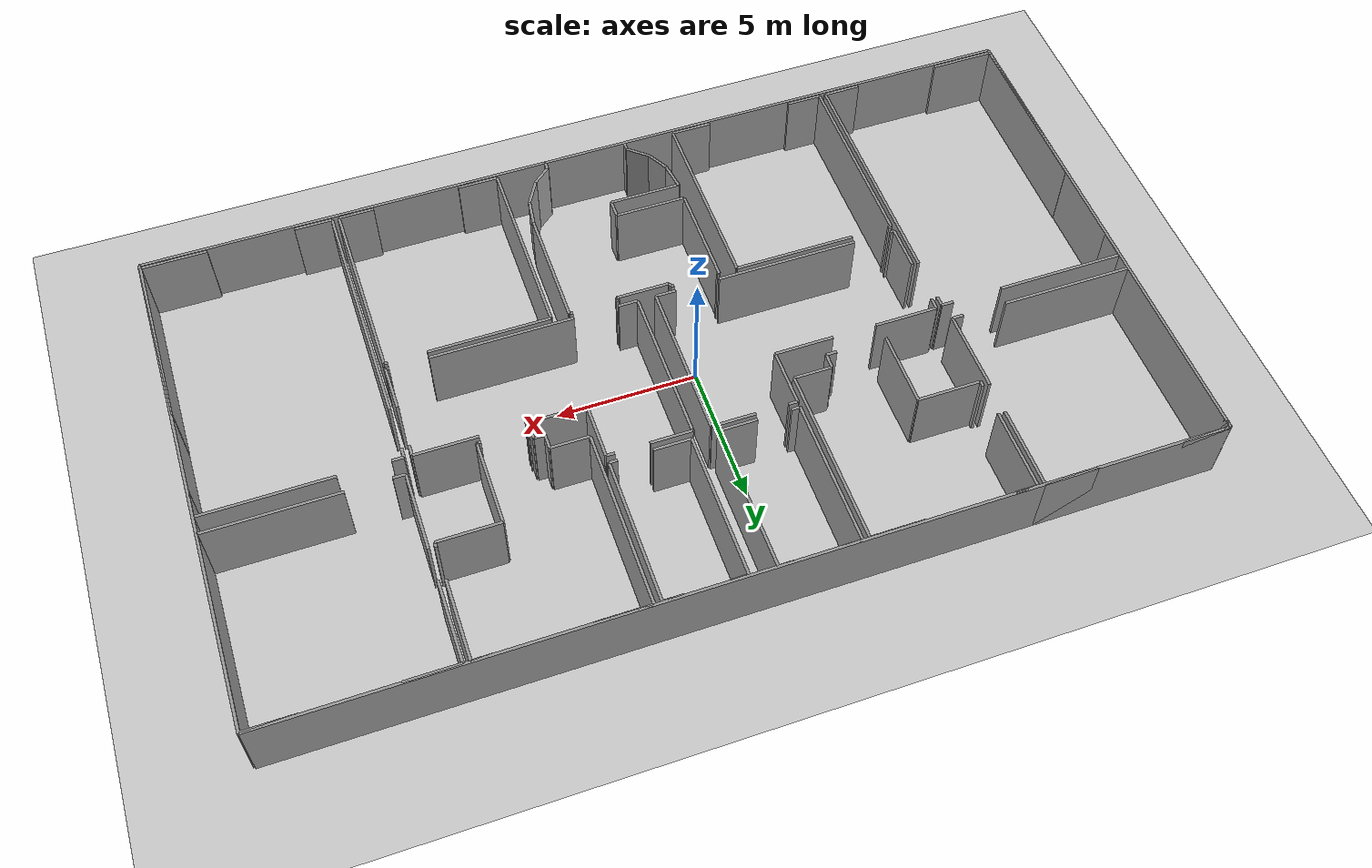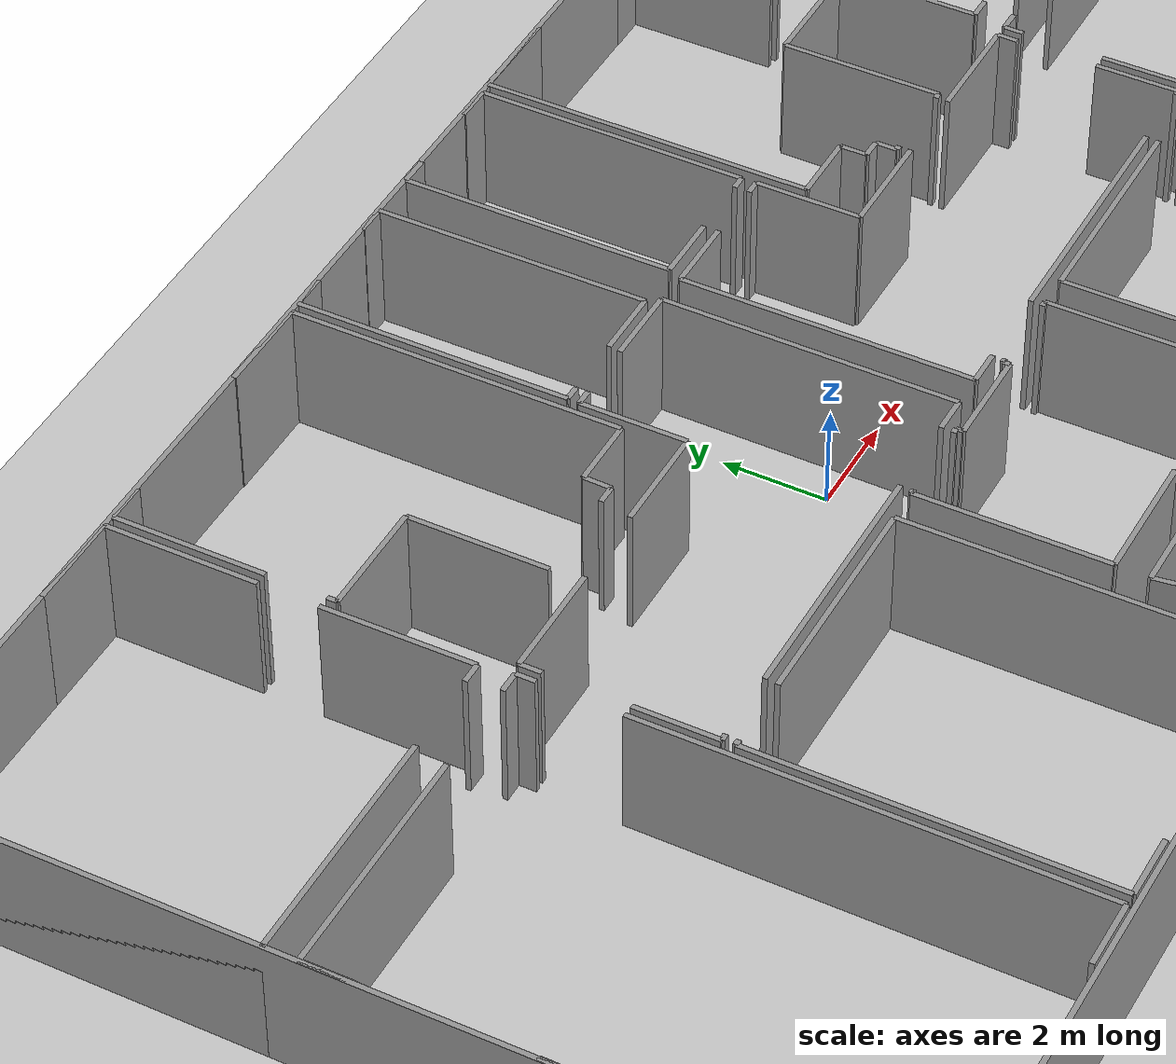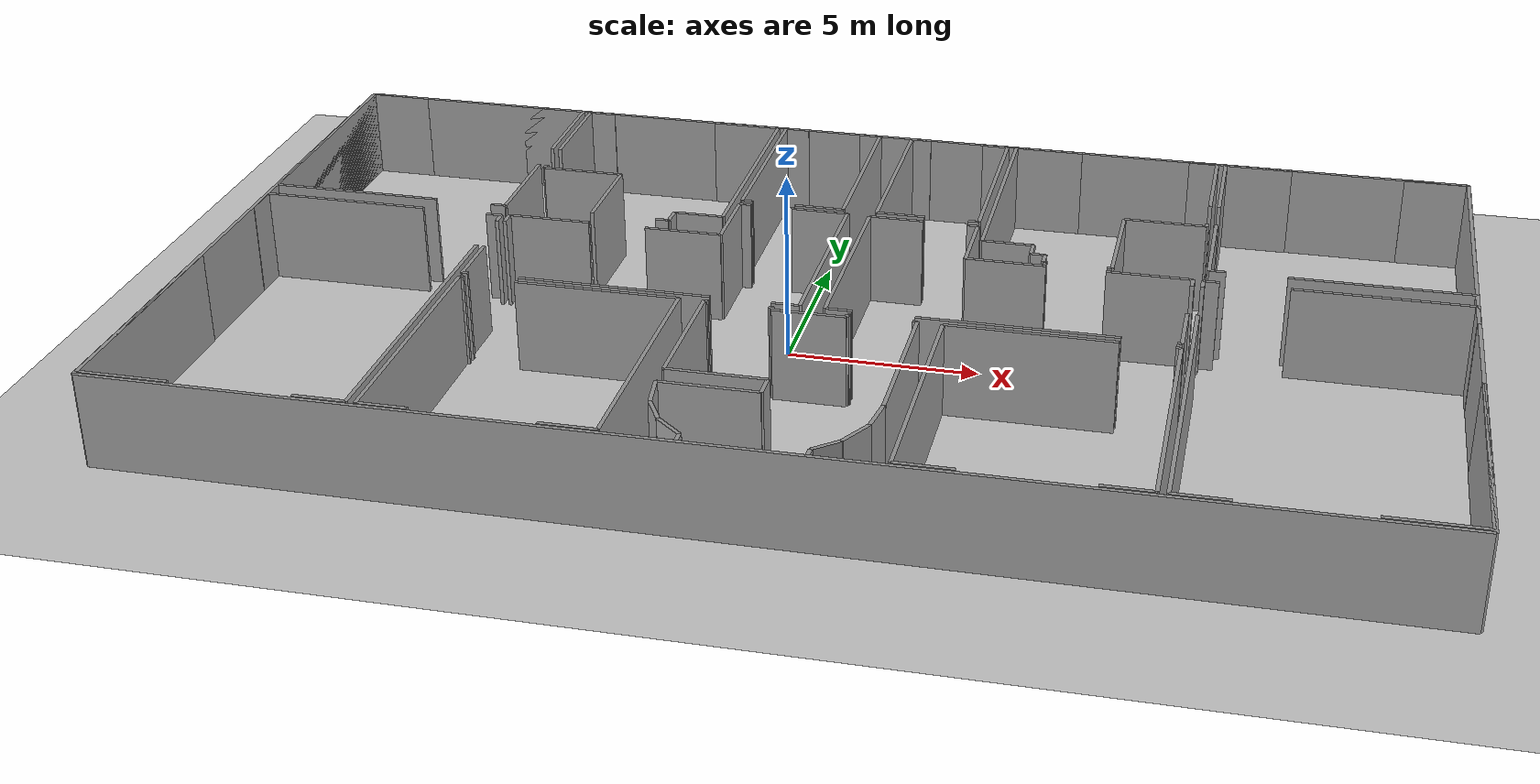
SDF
<sdf version="1.6">
  <world name="default">
    <light name="sun" type="directional">
      <cast_shadows>1</cast_shadows>
      <pose frame="">0 0 10 0 -0 0</pose>
      <diffuse>0.8 0.8 0.8 1</diffuse>
      <specular>0.1 0.1 0.1 1</specular>
      <attenuation>
        <range>1000</range>
        <constant>0.9</constant>
        <linear>0.01</linear>
        <quadratic>0.001</quadratic>
      </attenuation>
      <direction>-0.5 0.5 -1</direction>
    </light>
    <model name="ground_plane">
      <static>1</static>
      <link name="link">
        <collision name="collision">
          <geometry>
            <plane>
              <normal>0 0 1</normal>
              <size>100 100</size>
            </plane>
          </geometry>
          <surface>
            <friction>
              <ode>
                <mu>100</mu>
                <mu2>50</mu2>
              </ode>
              <torsional>
                <ode />
              </torsional>
            </friction>
            <contact>
              <ode />
            </contact>
            <bounce />
          </surface>
          <max_contacts>10</max_contacts>
        </collision>
        <visual name="visual">
          <cast_shadows>0</cast_shadows>
          <geometry>
            <plane>
              <normal>0 0 1</normal>
              <size>100 100</size>
            </plane>
          </geometry>
          <material>
            <script>
              <uri>file://media/materials/scripts/gazebo.material</uri>
              <name>Gazebo/Grey</name>
            </script>
          </material>
        </visual>
        <self_collide>0</self_collide>
        <kinematic>0</kinematic>
        <gravity>1</gravity>
      </link>
    </model>
    <gravity>0 0 -9.8</gravity>
    <magnetic_field>6e-06 2.3e-05 -4.2e-05</magnetic_field>
    <atmosphere type="adiabatic" />
    <physics default="0" name="default_physics" type="ode">
      <max_step_size>0.001</max_step_size>
      <real_time_factor>1</real_time_factor>
      <real_time_update_rate>1000</real_time_update_rate>
    </physics>
    <scene>
      <ambient>0.4 0.4 0.4 1</ambient>
      <background>0.7 0.7 0.7 1</background>
      <shadows>1</shadows>
    </scene>
    <spherical_coordinates>
      <surface_model>EARTH_WGS84</surface_model>
      <latitude_deg>0</latitude_deg>
      <longitude_deg>0</longitude_deg>
      <elevation>0</elevation>
      <heading_deg>0</heading_deg>
    </spherical_coordinates>
  <model name="0510034860_A-40">
		<static>1</static>
		<link name="Wall_0">
			<collision name="Wall_0_Collision">
				<geometry>
					<box>
						<size>0.409606582147 0.1 2.5</size>
					</box>
				</geometry>
				<pose frame="">0.204803291073 0 1.25 0 0 0</pose>
			</collision>
			<visual name="Wall_0_Visual">
				<pose frame="">0.204803291073 0 1.25 0 0 0</pose>
				<geometry>
					<box>
						<size>0.409606582147 0.1 2.5</size>
					</box>
				</geometry>
				<material>
					<script>
						<uri>file://media/materials/scripts/gazebo.material</uri>
						<name>Gazebo/Grey</name>
					</script>
					<ambient>1 1 1 1</ambient>
				</material>
			</visual>
			<pose frame="">6.63522032543 -6.92560168109 0 0 0 3.14159265359</pose>
		</link>
		<link name="Wall_1">
			<collision name="Wall_1_Collision">
				<geometry>
					<box>
						<size>4.66057631875 0.1 2.5</size>
					</box>
				</geometry>
				<pose frame="">2.33028815937 0 1.25 0 0 0</pose>
			</collision>
			<visual name="Wall_1_Visual">
				<pose frame="">2.33028815937 0 1.25 0 0 0</pose>
				<geometry>
					<box>
						<size>4.66057631875 0.1 2.5</size>
					</box>
				</geometry>
				<material>
					<script>
						<uri>file://media/materials/scripts/gazebo.material</uri>
						<name>Gazebo/Grey</name>
					</script>
					<ambient>1 1 1 1</ambient>
				</material>
			</visual>
			<pose frame="">4.66057631875 -6.92560168109 0 0 0 3.14159265359</pose>
		</link>
		<link name="Wall_2">
			<collision name="Wall_2_Collision">
				<geometry>
					<box>
						<size>6.92560168109 0.1 2.5</size>
					</box>
				</geometry>
				<pose frame="">3.46280084054 0 1.25 0 0 0</pose>
			</collision>
			<visual name="Wall_2_Visual">
				<pose frame="">3.46280084054 0 1.25 0 0 0</pose>
				<geometry>
					<box>
						<size>6.92560168109 0.1 2.5</size>
					</box>
				</geometry>
				<material>
					<script>
						<uri>file://media/materials/scripts/gazebo.material</uri>
						<name>Gazebo/Grey</name>
					</script>
					<ambient>1 1 1 1</ambient>
				</material>
			</visual>
			<pose frame="">0.0 -6.92560168109 0 0 0 1.57079632679</pose>
		</link>
		<link name="Wall_3">
			<collision name="Wall_3_Collision">
				<geometry>
					<box>
						<size>1.72768653542 0.1 2.5</size>
					</box>
				</geometry>
				<pose frame="">0.863843267711 0 1.25 0 0 0</pose>
			</collision>
			<visual name="Wall_3_Visual">
				<pose frame="">0.863843267711 0 1.25 0 0 0</pose>
				<geometry>
					<box>
						<size>1.72768653542 0.1 2.5</size>
					</box>
				</geometry>
				<material>
					<script>
						<uri>file://media/materials/scripts/gazebo.material</uri>
						<name>Gazebo/Grey</name>
					</script>
					<ambient>1 1 1 1</ambient>
				</material>
			</visual>
			<pose frame="">0.0 -0.0 0 0 0 0.0</pose>
		</link>
		<link name="Wall_4">
			<collision name="Wall_4_Collision">
				<geometry>
					<box>
						<size>1.86633823651 0.1 2.5</size>
					</box>
				</geometry>
				<pose frame="">0.933169118254 0 1.25 0 0 0</pose>
			</collision>
			<visual name="Wall_4_Visual">
				<pose frame="">0.933169118254 0 1.25 0 0 0</pose>
				<geometry>
					<box>
						<size>1.86633823651 0.1 2.5</size>
					</box>
				</geometry>
				<material>
					<script>
						<uri>file://media/materials/scripts/gazebo.material</uri>
						<name>Gazebo/Grey</name>
					</script>
					<ambient>1 1 1 1</ambient>
				</material>
			</visual>
			<pose frame="">4.74907470305 -0.0 0 0 0 0.0</pose>
		</link>
		<link name="Wall_5">
			<collision name="Wall_5_Collision">
				<geometry>
					<box>
						<size>2.90813055099 0.1 2.5</size>
					</box>
				</geometry>
				<pose frame="">1.45406527549 0 1.25 0 0 0</pose>
			</collision>
			<visual name="Wall_5_Visual">
				<pose frame="">1.45406527549 0 1.25 0 0 0</pose>
				<geometry>
					<box>
						<size>2.90813055099 0.1 2.5</size>
					</box>
				</geometry>
				<material>
					<script>
						<uri>file://media/materials/scripts/gazebo.material</uri>
						<name>Gazebo/Grey</name>
					</script>
					<ambient>1 1 1 1</ambient>
				</material>
			</visual>
			<pose frame="">6.61541293956 -0.0 0 0 0 -1.57079632679</pose>
		</link>
		<link name="Wall_6">
			<collision name="Wall_6_Collision">
				<geometry>
					<box>
						<size>2.8801381985 0.1 2.5</size>
					</box>
				</geometry>
				<pose frame="">1.44006909925 0 1.25 0 0 0</pose>
			</collision>
			<visual name="Wall_6_Visual">
				<pose frame="">1.44006909925 0 1.25 0 0 0</pose>
				<geometry>
					<box>
						<size>2.8801381985 0.1 2.5</size>
					</box>
				</geometry>
				<material>
					<script>
						<uri>file://media/materials/scripts/gazebo.material</uri>
						<name>Gazebo/Grey</name>
					</script>
					<ambient>1 1 1 1</ambient>
				</material>
			</visual>
			<pose frame="">6.61541293956 -4.04553159342 0 0 0 -1.56391903805</pose>
		</link>
		<link name="Wall_7">
			<collision name="Wall_7_Collision">
				<geometry>
					<box>
						<size>0.36275449634 0.1 2.5</size>
					</box>
				</geometry>
				<pose frame="">0.18137724817 0 1.25 0 0 0</pose>
			</collision>
			<visual name="Wall_7_Visual">
				<pose frame="">0.18137724817 0 1.25 0 0 0</pose>
				<geometry>
					<box>
						<size>0.36275449634 0.1 2.5</size>
					</box>
				</geometry>
				<material>
					<script>
						<uri>file://media/materials/scripts/gazebo.material</uri>
						<name>Gazebo/Grey</name>
					</script>
					<ambient>1 1 1 1</ambient>
				</material>
			</visual>
			<pose frame="">11.2159322486 -6.90388973889 0 0 0 3.14159265359</pose>
		</link>
		<link name="Wall_8">
			<collision name="Wall_8_Collision">
				<geometry>
					<box>
						<size>2.65406273609 0.1 2.5</size>
					</box>
				</geometry>
				<pose frame="">1.32703136804 0 1.25 0 0 0</pose>
			</collision>
			<visual name="Wall_8_Visual">
				<pose frame="">1.32703136804 0 1.25 0 0 0</pose>
				<geometry>
					<box>
						<size>2.65406273609 0.1 2.5</size>
					</box>
				</geometry>
				<material>
					<script>
						<uri>file://media/materials/scripts/gazebo.material</uri>
						<name>Gazebo/Grey</name>
					</script>
					<ambient>1 1 1 1</ambient>
				</material>
			</visual>
			<pose frame="">9.07444910708 -6.90388973889 0 0 0 1.57079632679</pose>
		</link>
		<link name="Wall_9">
			<collision name="Wall_9_Collision">
				<geometry>
					<box>
						<size>2.22731514694 0.1 2.5</size>
					</box>
				</geometry>
				<pose frame="">1.11365757347 0 1.25 0 0 0</pose>
			</collision>
			<visual name="Wall_9_Visual">
				<pose frame="">1.11365757347 0 1.25 0 0 0</pose>
				<geometry>
					<box>
						<size>2.22731514694 0.1 2.5</size>
					</box>
				</geometry>
				<material>
					<script>
						<uri>file://media/materials/scripts/gazebo.material</uri>
						<name>Gazebo/Grey</name>
					</script>
					<ambient>1 1 1 1</ambient>
				</material>
			</visual>
			<pose frame="">9.07444910708 -4.2498270028 0 0 0 3.14159265359</pose>
		</link>
		<link name="Wall_10">
			<collision name="Wall_10_Collision">
				<geometry>
					<box>
						<size>0.191979278427 0.1 2.5</size>
					</box>
				</geometry>
				<pose frame="">0.0959896392135 0 1.25 0 0 0</pose>
			</collision>
			<visual name="Wall_10_Visual">
				<pose frame="">0.0959896392135 0 1.25 0 0 0</pose>
				<geometry>
					<box>
						<size>0.191979278427 0.1 2.5</size>
					</box>
				</geometry>
				<material>
					<script>
						<uri>file://media/materials/scripts/gazebo.material</uri>
						<name>Gazebo/Grey</name>
					</script>
					<ambient>1 1 1 1</ambient>
				</material>
			</visual>
			<pose frame="">6.84713396014 -4.2498270028 0 0 0 1.57079632679</pose>
		</link>
		<link name="Wall_11">
			<collision name="Wall_11_Collision">
				<geometry>
					<box>
						<size>2.89010075103 0.1 2.5</size>
					</box>
				</geometry>
				<pose frame="">1.44505037552 0 1.25 0 0 0</pose>
			</collision>
			<visual name="Wall_11_Visual">
				<pose frame="">1.44505037552 0 1.25 0 0 0</pose>
				<geometry>
					<box>
						<size>2.89010075103 0.1 2.5</size>
					</box>
				</geometry>
				<material>
					<script>
						<uri>file://media/materials/scripts/gazebo.material</uri>
						<name>Gazebo/Grey</name>
					</script>
					<ambient>1 1 1 1</ambient>
				</material>
			</visual>
			<pose frame="">6.84713396014 -2.91066995943 0 0 0 1.57079632679</pose>
		</link>
		<link name="Wall_12">
			<collision name="Wall_12_Collision">
				<geometry>
					<box>
						<size>0.758267361618 0.1 2.5</size>
					</box>
				</geometry>
				<pose frame="">0.379133680809 0 1.25 0 0 0</pose>
			</collision>
			<visual name="Wall_12_Visual">
				<pose frame="">0.379133680809 0 1.25 0 0 0</pose>
				<geometry>
					<box>
						<size>0.758267361618 0.1 2.5</size>
					</box>
				</geometry>
				<material>
					<script>
						<uri>file://media/materials/scripts/gazebo.material</uri>
						<name>Gazebo/Grey</name>
					</script>
					<ambient>1 1 1 1</ambient>
				</material>
			</visual>
			<pose frame="">6.84713396014 -0.0205692084029 0 0 0 0.0</pose>
		</link>
		<link name="Wall_13">
			<collision name="Wall_13_Collision">
				<geometry>
					<box>
						<size>1.90696877162 0.1 2.5</size>
					</box>
				</geometry>
				<pose frame="">0.953484385812 0 1.25 0 0 0</pose>
			</collision>
			<visual name="Wall_13_Visual">
				<pose frame="">0.953484385812 0 1.25 0 0 0</pose>
				<geometry>
					<box>
						<size>1.90696877162 0.1 2.5</size>
					</box>
				</geometry>
				<material>
					<script>
						<uri>file://media/materials/scripts/gazebo.material</uri>
						<name>Gazebo/Grey</name>
					</script>
					<ambient>1 1 1 1</ambient>
				</material>
			</visual>
			<pose frame="">10.6670391132 -0.0205692084029 0 0 0 0.0</pose>
		</link>
		<link name="Wall_14">
			<collision name="Wall_14_Collision">
				<geometry>
					<box>
						<size>6.35677418945 0.1 2.5</size>
					</box>
				</geometry>
				<pose frame="">3.17838709473 0 1.25 0 0 0</pose>
			</collision>
			<visual name="Wall_14_Visual">
				<pose frame="">3.17838709473 0 1.25 0 0 0</pose>
				<geometry>
					<box>
						<size>6.35677418945 0.1 2.5</size>
					</box>
				</geometry>
				<material>
					<script>
						<uri>file://media/materials/scripts/gazebo.material</uri>
						<name>Gazebo/Grey</name>
					</script>
					<ambient>1 1 1 1</ambient>
				</material>
			</visual>
			<pose frame="">12.5740078849 -0.0205692084029 0 0 0 -1.57079632679</pose>
		</link>
		<link name="Wall_15">
			<collision name="Wall_15_Collision">
				<geometry>
					<box>
						<size>1.3387761321 0.1 2.5</size>
					</box>
				</geometry>
				<pose frame="">0.66938806605 0 1.25 0 0 0</pose>
			</collision>
			<visual name="Wall_15_Visual">
				<pose frame="">0.66938806605 0 1.25 0 0 0</pose>
				<geometry>
					<box>
						<size>1.3387761321 0.1 2.5</size>
					</box>
				</geometry>
				<material>
					<script>
						<uri>file://media/materials/scripts/gazebo.material</uri>
						<name>Gazebo/Grey</name>
					</script>
					<ambient>1 1 1 1</ambient>
				</material>
			</visual>
			<pose frame="">12.5740078849 -6.37734339786 0 0 0 3.14159265359</pose>
		</link>
		<link name="Wall_16">
			<collision name="Wall_16_Collision">
				<geometry>
					<box>
						<size>0.526899914703 0.1 2.5</size>
					</box>
				</geometry>
				<pose frame="">0.263449957351 0 1.25 0 0 0</pose>
			</collision>
			<visual name="Wall_16_Visual">
				<pose frame="">0.263449957351 0 1.25 0 0 0</pose>
				<geometry>
					<box>
						<size>0.526899914703 0.1 2.5</size>
					</box>
				</geometry>
				<material>
					<script>
						<uri>file://media/materials/scripts/gazebo.material</uri>
						<name>Gazebo/Grey</name>
					</script>
					<ambient>1 1 1 1</ambient>
				</material>
			</visual>
			<pose frame="">11.2352317528 -6.37734339786 0 0 0 -1.60743292845</pose>
		</link>
		<link name="Wall_17">
			<collision name="Wall_17_Collision">
				<geometry>
					<box>
						<size>1.32493635608 0.1 2.5</size>
					</box>
				</geometry>
				<pose frame="">0.662468178038 0 1.25 0 0 0</pose>
			</collision>
			<visual name="Wall_17_Visual">
				<pose frame="">0.662468178038 0 1.25 0 0 0</pose>
				<geometry>
					<box>
						<size>1.32493635608 0.1 2.5</size>
					</box>
				</geometry>
				<material>
					<script>
						<uri>file://media/materials/scripts/gazebo.material</uri>
						<name>Gazebo/Grey</name>
					</script>
					<ambient>1 1 1 1</ambient>
				</material>
			</visual>
			<pose frame="">6.73362240266 -18.0047867849 0 0 0 3.14159265359</pose>
		</link>
		<link name="Wall_18">
			<collision name="Wall_18_Collision">
				<geometry>
					<box>
						<size>2.29156218059 0.1 2.5</size>
					</box>
				</geometry>
				<pose frame="">1.1457810903 0 1.25 0 0 0</pose>
			</collision>
			<visual name="Wall_18_Visual">
				<pose frame="">1.1457810903 0 1.25 0 0 0</pose>
				<geometry>
					<box>
						<size>2.29156218059 0.1 2.5</size>
					</box>
				</geometry>
				<material>
					<script>
						<uri>file://media/materials/scripts/gazebo.material</uri>
						<name>Gazebo/Grey</name>
					</script>
					<ambient>1 1 1 1</ambient>
				</material>
			</visual>
			<pose frame="">2.30286254817 -18.0047867849 0 0 0 3.14159265359</pose>
		</link>
		<link name="Wall_19">
			<collision name="Wall_19_Collision">
				<geometry>
					<box>
						<size>6.42571912873 0.1 2.5</size>
					</box>
				</geometry>
				<pose frame="">3.21285956436 0 1.25 0 0 0</pose>
			</collision>
			<visual name="Wall_19_Visual">
				<pose frame="">3.21285956436 0 1.25 0 0 0</pose>
				<geometry>
					<box>
						<size>6.42571912873 0.1 2.5</size>
					</box>
				</geometry>
				<material>
					<script>
						<uri>file://media/materials/scripts/gazebo.material</uri>
						<name>Gazebo/Grey</name>
					</script>
					<ambient>1 1 1 1</ambient>
				</material>
			</visual>
			<pose frame="">0.0113003675794 -18.0047867849 0 0 0 1.57079632679</pose>
		</link>
		<link name="Wall_20">
			<collision name="Wall_20_Collision">
				<geometry>
					<box>
						<size>0.987322003339 0.1 2.5</size>
					</box>
				</geometry>
				<pose frame="">0.49366100167 0 1.25 0 0 0</pose>
			</collision>
			<visual name="Wall_20_Visual">
				<pose frame="">0.49366100167 0 1.25 0 0 0</pose>
				<geometry>
					<box>
						<size>0.987322003339 0.1 2.5</size>
					</box>
				</geometry>
				<material>
					<script>
						<uri>file://media/materials/scripts/gazebo.material</uri>
						<name>Gazebo/Grey</name>
					</script>
					<ambient>1 1 1 1</ambient>
				</material>
			</visual>
			<pose frame="">0.0113003675794 -8.53723725058 0 0 0 1.57079632679</pose>
		</link>
		<link name="Wall_21">
			<collision name="Wall_21_Collision">
				<geometry>
					<box>
						<size>4.51824247542 0.1 2.5</size>
					</box>
				</geometry>
				<pose frame="">2.25912123771 0 1.25 0 0 0</pose>
			</collision>
			<visual name="Wall_21_Visual">
				<pose frame="">2.25912123771 0 1.25 0 0 0</pose>
				<geometry>
					<box>
						<size>4.51824247542 0.1 2.5</size>
					</box>
				</geometry>
				<material>
					<script>
						<uri>file://media/materials/scripts/gazebo.material</uri>
						<name>Gazebo/Grey</name>
					</script>
					<ambient>1 1 1 1</ambient>
				</material>
			</visual>
			<pose frame="">0.0113003675794 -7.54991524724 0 0 0 0.0</pose>
		</link>
		<link name="Wall_22">
			<collision name="Wall_22_Collision">
				<geometry>
					<box>
						<size>0.424970003238 0.1 2.5</size>
					</box>
				</geometry>
				<pose frame="">0.212485001619 0 1.25 0 0 0</pose>
			</collision>
			<visual name="Wall_22_Visual">
				<pose frame="">0.212485001619 0 1.25 0 0 0</pose>
				<geometry>
					<box>
						<size>0.424970003238 0.1 2.5</size>
					</box>
				</geometry>
				<material>
					<script>
						<uri>file://media/materials/scripts/gazebo.material</uri>
						<name>Gazebo/Grey</name>
					</script>
					<ambient>1 1 1 1</ambient>
				</material>
			</visual>
			<pose frame="">6.31906397405 -7.54991524724 0 0 0 0.0</pose>
		</link>
		<link name="Wall_23">
			<collision name="Wall_23_Collision">
				<geometry>
					<box>
						<size>0.370245751252 0.1 2.5</size>
					</box>
				</geometry>
				<pose frame="">0.185122875626 0 1.25 0 0 0</pose>
			</collision>
			<visual name="Wall_23_Visual">
				<pose frame="">0.185122875626 0 1.25 0 0 0</pose>
				<geometry>
					<box>
						<size>0.370245751252 0.1 2.5</size>
					</box>
				</geometry>
				<material>
					<script>
						<uri>file://media/materials/scripts/gazebo.material</uri>
						<name>Gazebo/Grey</name>
					</script>
					<ambient>1 1 1 1</ambient>
				</material>
			</visual>
			<pose frame="">6.74403397728 -7.54991524724 0 0 0 -1.57079632679</pose>
		</link>
		<link name="Wall_24">
			<collision name="Wall_24_Collision">
				<geometry>
					<box>
						<size>8.52378474456 0.1 2.5</size>
					</box>
				</geometry>
				<pose frame="">4.26189237228 0 1.25 0 0 0</pose>
			</collision>
			<visual name="Wall_24_Visual">
				<pose frame="">4.26189237228 0 1.25 0 0 0</pose>
				<geometry>
					<box>
						<size>8.52378474456 0.1 2.5</size>
					</box>
				</geometry>
				<material>
					<script>
						<uri>file://media/materials/scripts/gazebo.material</uri>
						<name>Gazebo/Grey</name>
					</script>
					<ambient>1 1 1 1</ambient>
				</material>
			</visual>
			<pose frame="">6.74403397728 -9.48100839909 0 0 0 -1.5720178003</pose>
		</link>
		<link name="Wall_25">
			<collision name="Wall_25_Collision">
				<geometry>
					<box>
						<size>1.43159151076 0.1 2.5</size>
					</box>
				</geometry>
				<pose frame="">0.715795755379 0 1.25 0 0 0</pose>
			</collision>
			<visual name="Wall_25_Visual">
				<pose frame="">0.715795755379 0 1.25 0 0 0</pose>
				<geometry>
					<box>
						<size>1.43159151076 0.1 2.5</size>
					</box>
				</geometry>
				<material>
					<script>
						<uri>file://media/materials/scripts/gazebo.material</uri>
						<name>Gazebo/Grey</name>
					</script>
					<ambient>1 1 1 1</ambient>
				</material>
			</visual>
			<pose frame="">12.7419897535 -18.0077071046 0 0 0 3.14159265359</pose>
		</link>
		<link name="Wall_26">
			<collision name="Wall_26_Collision">
				<geometry>
					<box>
						<size>1.24862713231 0.1 2.5</size>
					</box>
				</geometry>
				<pose frame="">0.624313566155 0 1.25 0 0 0</pose>
			</collision>
			<visual name="Wall_26_Visual">
				<pose frame="">0.624313566155 0 1.25 0 0 0</pose>
				<geometry>
					<box>
						<size>1.24862713231 0.1 2.5</size>
					</box>
				</geometry>
				<material>
					<script>
						<uri>file://media/materials/scripts/gazebo.material</uri>
						<name>Gazebo/Grey</name>
					</script>
					<ambient>1 1 1 1</ambient>
				</material>
			</visual>
			<pose frame="">8.21777966823 -18.0077071046 0 0 0 3.14159265359</pose>
		</link>
		<link name="Wall_27">
			<collision name="Wall_27_Collision">
				<geometry>
					<box>
						<size>6.6915951929 0.1 2.5</size>
					</box>
				</geometry>
				<pose frame="">3.34579759645 0 1.25 0 0 0</pose>
			</collision>
			<visual name="Wall_27_Visual">
				<pose frame="">3.34579759645 0 1.25 0 0 0</pose>
				<geometry>
					<box>
						<size>6.6915951929 0.1 2.5</size>
					</box>
				</geometry>
				<material>
					<script>
						<uri>file://media/materials/scripts/gazebo.material</uri>
						<name>Gazebo/Grey</name>
					</script>
					<ambient>1 1 1 1</ambient>
				</material>
			</visual>
			<pose frame="">6.96915253592 -18.0077071046 0 0 0 1.57079632679</pose>
		</link>
		<link name="Wall_28">
			<collision name="Wall_28_Collision">
				<geometry>
					<box>
						<size>0.118336433528 0.1 2.5</size>
					</box>
				</geometry>
				<pose frame="">0.0591682167639 0 1.25 0 0 0</pose>
			</collision>
			<visual name="Wall_28_Visual">
				<pose frame="">0.0591682167639 0 1.25 0 0 0</pose>
				<geometry>
					<box>
						<size>0.118336433528 0.1 2.5</size>
					</box>
				</geometry>
				<material>
					<script>
						<uri>file://media/materials/scripts/gazebo.material</uri>
						<name>Gazebo/Grey</name>
					</script>
					<ambient>1 1 1 1</ambient>
				</material>
			</visual>
			<pose frame="">6.96915253592 -11.3161119117 0 0 0 0.0</pose>
		</link>
		<link name="Wall_29">
			<collision name="Wall_29_Collision">
				<geometry>
					<box>
						<size>4.2994724379 0.1 2.5</size>
					</box>
				</geometry>
				<pose frame="">2.14973621895 0 1.25 0 0 0</pose>
			</collision>
			<visual name="Wall_29_Visual">
				<pose frame="">2.14973621895 0 1.25 0 0 0</pose>
				<geometry>
					<box>
						<size>4.2994724379 0.1 2.5</size>
					</box>
				</geometry>
				<material>
					<script>
						<uri>file://media/materials/scripts/gazebo.material</uri>
						<name>Gazebo/Grey</name>
					</script>
					<ambient>1 1 1 1</ambient>
				</material>
			</visual>
			<pose frame="">8.43667667617 -11.3161119117 0 0 0 0.0</pose>
		</link>
		<link name="Wall_30">
			<collision name="Wall_30_Collision">
				<geometry>
					<box>
						<size>6.69159774185 0.1 2.5</size>
					</box>
				</geometry>
				<pose frame="">3.34579887092 0 1.25 0 0 0</pose>
			</collision>
			<visual name="Wall_30_Visual">
				<pose frame="">3.34579887092 0 1.25 0 0 0</pose>
				<geometry>
					<box>
						<size>6.69159774185 0.1 2.5</size>
					</box>
				</geometry>
				<material>
					<script>
						<uri>file://media/materials/scripts/gazebo.material</uri>
						<name>Gazebo/Grey</name>
					</script>
					<ambient>1 1 1 1</ambient>
				</material>
			</visual>
			<pose frame="">12.7361491141 -11.3161119117 0 0 0 -1.56992349487</pose>
		</link>
		<link name="Wall_31">
			<collision name="Wall_31_Collision">
				<geometry>
					<box>
						<size>0.718779560301 0.1 2.5</size>
					</box>
				</geometry>
				<pose frame="">0.359389780151 0 1.25 0 0 0</pose>
			</collision>
			<visual name="Wall_31_Visual">
				<pose frame="">0.359389780151 0 1.25 0 0 0</pose>
				<geometry>
					<box>
						<size>0.718779560301 0.1 2.5</size>
					</box>
				</geometry>
				<material>
					<script>
						<uri>file://media/materials/scripts/gazebo.material</uri>
						<name>Gazebo/Grey</name>
					</script>
					<ambient>1 1 1 1</ambient>
				</material>
			</visual>
			<pose frame="">15.7676949155 -11.0781693405 0 0 0 3.14159265359</pose>
		</link>
		<link name="Wall_32">
			<collision name="Wall_32_Collision">
				<geometry>
					<box>
						<size>5.0091101278 0.1 2.5</size>
					</box>
				</geometry>
				<pose frame="">2.5045550639 0 1.25 0 0 0</pose>
			</collision>
			<visual name="Wall_32_Visual">
				<pose frame="">2.5045550639 0 1.25 0 0 0</pose>
				<geometry>
					<box>
						<size>5.0091101278 0.1 2.5</size>
					</box>
				</geometry>
				<material>
					<script>
						<uri>file://media/materials/scripts/gazebo.material</uri>
						<name>Gazebo/Grey</name>
					</script>
					<ambient>1 1 1 1</ambient>
				</material>
			</visual>
			<pose frame="">13.4707999771 -11.0781693405 0 0 0 3.14159265359</pose>
		</link>
		<link name="Wall_33">
			<collision name="Wall_33_Collision">
				<geometry>
					<box>
						<size>0.141952932064 0.1 2.5</size>
					</box>
				</geometry>
				<pose frame="">0.0709764660322 0 1.25 0 0 0</pose>
			</collision>
			<visual name="Wall_33_Visual">
				<pose frame="">0.0709764660322 0 1.25 0 0 0</pose>
				<geometry>
					<box>
						<size>0.141952932064 0.1 2.5</size>
					</box>
				</geometry>
				<material>
					<script>
						<uri>file://media/materials/scripts/gazebo.material</uri>
						<name>Gazebo/Grey</name>
					</script>
					<ambient>1 1 1 1</ambient>
				</material>
			</visual>
			<pose frame="">7.1009478342 -11.0781693405 0 0 0 3.14159265359</pose>
		</link>
		<link name="Wall_34">
			<collision name="Wall_34_Collision">
				<geometry>
					<box>
						<size>1.58052781605 0.1 2.5</size>
					</box>
				</geometry>
				<pose frame="">0.790263908023 0 1.25 0 0 0</pose>
			</collision>
			<visual name="Wall_34_Visual">
				<pose frame="">0.790263908023 0 1.25 0 0 0</pose>
				<geometry>
					<box>
						<size>1.58052781605 0.1 2.5</size>
					</box>
				</geometry>
				<material>
					<script>
						<uri>file://media/materials/scripts/gazebo.material</uri>
						<name>Gazebo/Grey</name>
					</script>
					<ambient>1 1 1 1</ambient>
				</material>
			</visual>
			<pose frame="">6.95899490214 -11.0781693405 0 0 0 1.57079632679</pose>
		</link>
		<link name="Wall_35">
			<collision name="Wall_35_Collision">
				<geometry>
					<box>
						<size>0.417478748326 0.1 2.5</size>
					</box>
				</geometry>
				<pose frame="">0.208739374163 0 1.25 0 0 0</pose>
			</collision>
			<visual name="Wall_35_Visual">
				<pose frame="">0.208739374163 0 1.25 0 0 0</pose>
				<geometry>
					<box>
						<size>0.417478748326 0.1 2.5</size>
					</box>
				</geometry>
				<material>
					<script>
						<uri>file://media/materials/scripts/gazebo.material</uri>
						<name>Gazebo/Grey</name>
					</script>
					<ambient>1 1 1 1</ambient>
				</material>
			</visual>
			<pose frame="">6.95899490214 -7.91152700978 0 0 0 1.57079632679</pose>
		</link>
		<link name="Wall_36">
			<collision name="Wall_36_Collision">
				<geometry>
					<box>
						<size>2.22071268498 0.1 2.5</size>
					</box>
				</geometry>
				<pose frame="">1.11035634249 0 1.25 0 0 0</pose>
			</collision>
			<visual name="Wall_36_Visual">
				<pose frame="">1.11035634249 0 1.25 0 0 0</pose>
				<geometry>
					<box>
						<size>2.22071268498 0.1 2.5</size>
					</box>
				</geometry>
				<material>
					<script>
						<uri>file://media/materials/scripts/gazebo.material</uri>
						<name>Gazebo/Grey</name>
					</script>
					<ambient>1 1 1 1</ambient>
				</material>
			</visual>
			<pose frame="">6.95899490214 -7.49404826146 0 0 0 0.0</pose>
		</link>
		<link name="Wall_37">
			<collision name="Wall_37_Collision">
				<geometry>
					<box>
						<size>2.06466603605 0.1 2.5</size>
					</box>
				</geometry>
				<pose frame="">1.03233301802 0 1.25 0 0 0</pose>
			</collision>
			<visual name="Wall_37_Visual">
				<pose frame="">1.03233301802 0 1.25 0 0 0</pose>
				<geometry>
					<box>
						<size>2.06466603605 0.1 2.5</size>
					</box>
				</geometry>
				<material>
					<script>
						<uri>file://media/materials/scripts/gazebo.material</uri>
						<name>Gazebo/Grey</name>
					</script>
					<ambient>1 1 1 1</ambient>
				</material>
			</visual>
			<pose frame="">10.7411898398 -7.49404826146 0 0 0 0.0</pose>
		</link>
		<link name="Wall_38">
			<collision name="Wall_38_Collision">
				<geometry>
					<box>
						<size>2.02886037698 0.1 2.5</size>
					</box>
				</geometry>
				<pose frame="">1.01443018849 0 1.25 0 0 0</pose>
			</collision>
			<visual name="Wall_38_Visual">
				<pose frame="">1.01443018849 0 1.25 0 0 0</pose>
				<geometry>
					<box>
						<size>2.02886037698 0.1 2.5</size>
					</box>
				</geometry>
				<material>
					<script>
						<uri>file://media/materials/scripts/gazebo.material</uri>
						<name>Gazebo/Grey</name>
					</script>
					<ambient>1 1 1 1</ambient>
				</material>
			</visual>
			<pose frame="">12.8058558759 -7.49404826146 0 0 0 1.57079632679</pose>
		</link>
		<link name="Wall_39">
			<collision name="Wall_39_Collision">
				<geometry>
					<box>
						<size>0.314632706311 0.1 2.5</size>
					</box>
				</geometry>
				<pose frame="">0.157316353156 0 1.25 0 0 0</pose>
			</collision>
			<visual name="Wall_39_Visual">
				<pose frame="">0.157316353156 0 1.25 0 0 0</pose>
				<geometry>
					<box>
						<size>0.314632706311 0.1 2.5</size>
					</box>
				</geometry>
				<material>
					<script>
						<uri>file://media/materials/scripts/gazebo.material</uri>
						<name>Gazebo/Grey</name>
					</script>
					<ambient>1 1 1 1</ambient>
				</material>
			</visual>
			<pose frame="">12.8058558759 -5.46518788448 0 0 0 0.0</pose>
		</link>
		<link name="Wall_40">
			<collision name="Wall_40_Collision">
				<geometry>
					<box>
						<size>1.53392967108 0.1 2.5</size>
					</box>
				</geometry>
				<pose frame="">0.766964835542 0 1.25 0 0 0</pose>
			</collision>
			<visual name="Wall_40_Visual">
				<pose frame="">0.766964835542 0 1.25 0 0 0</pose>
				<geometry>
					<box>
						<size>1.53392967108 0.1 2.5</size>
					</box>
				</geometry>
				<material>
					<script>
						<uri>file://media/materials/scripts/gazebo.material</uri>
						<name>Gazebo/Grey</name>
					</script>
					<ambient>1 1 1 1</ambient>
				</material>
			</visual>
			<pose frame="">14.2590323584 -5.46518788448 0 0 0 0.0</pose>
		</link>
		<link name="Wall_41">
			<collision name="Wall_41_Collision">
				<geometry>
					<box>
						<size>5.61303832626 0.1 2.5</size>
					</box>
				</geometry>
				<pose frame="">2.80651916313 0 1.25 0 0 0</pose>
			</collision>
			<visual name="Wall_41_Visual">
				<pose frame="">2.80651916313 0 1.25 0 0 0</pose>
				<geometry>
					<box>
						<size>5.61303832626 0.1 2.5</size>
					</box>
				</geometry>
				<material>
					<script>
						<uri>file://media/materials/scripts/gazebo.material</uri>
						<name>Gazebo/Grey</name>
					</script>
					<ambient>1 1 1 1</ambient>
				</material>
			</visual>
			<pose frame="">15.7929620295 -5.46518788448 0 0 0 -1.57529784592</pose>
		</link>
		<link name="Wall_42">
			<collision name="Wall_42_Collision">
				<geometry>
					<box>
						<size>1.33522096028 0.1 2.5</size>
					</box>
				</geometry>
				<pose frame="">0.667610480139 0 1.25 0 0 0</pose>
			</collision>
			<visual name="Wall_42_Visual">
				<pose frame="">0.667610480139 0 1.25 0 0 0</pose>
				<geometry>
					<box>
						<size>1.33522096028 0.1 2.5</size>
					</box>
				</geometry>
				<material>
					<script>
						<uri>file://media/materials/scripts/gazebo.material</uri>
						<name>Gazebo/Grey</name>
					</script>
					<ambient>1 1 1 1</ambient>
				</material>
			</visual>
			<pose frame="">15.62472622 -5.23994235543 0 0 0 3.14159265359</pose>
		</link>
		<link name="Wall_43">
			<collision name="Wall_43_Collision">
				<geometry>
					<box>
						<size>0.304855983799 0.1 2.5</size>
					</box>
				</geometry>
				<pose frame="">0.152427991899 0 1.25 0 0 0</pose>
			</collision>
			<visual name="Wall_43_Visual">
				<pose frame="">0.152427991899 0 1.25 0 0 0</pose>
				<geometry>
					<box>
						<size>0.304855983799 0.1 2.5</size>
					</box>
				</geometry>
				<material>
					<script>
						<uri>file://media/materials/scripts/gazebo.material</uri>
						<name>Gazebo/Grey</name>
					</script>
					<ambient>1 1 1 1</ambient>
				</material>
			</visual>
			<pose frame="">13.1179491737 -5.23994235543 0 0 0 3.14159265359</pose>
		</link>
		<link name="Wall_44">
			<collision name="Wall_44_Collision">
				<geometry>
					<box>
						<size>5.23054654418 0.1 2.5</size>
					</box>
				</geometry>
				<pose frame="">2.61527327209 0 1.25 0 0 0</pose>
			</collision>
			<visual name="Wall_44_Visual">
				<pose frame="">2.61527327209 0 1.25 0 0 0</pose>
				<geometry>
					<box>
						<size>5.23054654418 0.1 2.5</size>
					</box>
				</geometry>
				<material>
					<script>
						<uri>file://media/materials/scripts/gazebo.material</uri>
						<name>Gazebo/Grey</name>
					</script>
					<ambient>1 1 1 1</ambient>
				</material>
			</visual>
			<pose frame="">12.8130931899 -5.23994235543 0 0 0 1.57079632679</pose>
		</link>
		<link name="Wall_45">
			<collision name="Wall_45_Collision">
				<geometry>
					<box>
						<size>0.684497546297 0.1 2.5</size>
					</box>
				</geometry>
				<pose frame="">0.342248773148 0 1.25 0 0 0</pose>
			</collision>
			<visual name="Wall_45_Visual">
				<pose frame="">0.342248773148 0 1.25 0 0 0</pose>
				<geometry>
					<box>
						<size>0.684497546297 0.1 2.5</size>
					</box>
				</geometry>
				<material>
					<script>
						<uri>file://media/materials/scripts/gazebo.material</uri>
						<name>Gazebo/Grey</name>
					</script>
					<ambient>1 1 1 1</ambient>
				</material>
			</visual>
			<pose frame="">12.8130931899 -0.00939581124577 0 0 0 0.0</pose>
		</link>
		<link name="Wall_46">
			<collision name="Wall_46_Collision">
				<geometry>
					<box>
						<size>0.588380936661 0.1 2.5</size>
					</box>
				</geometry>
				<pose frame="">0.29419046833 0 1.25 0 0 0</pose>
			</collision>
			<visual name="Wall_46_Visual">
				<pose frame="">0.29419046833 0 1.25 0 0 0</pose>
				<geometry>
					<box>
						<size>0.588380936661 0.1 2.5</size>
					</box>
				</geometry>
				<material>
					<script>
						<uri>file://media/materials/scripts/gazebo.material</uri>
						<name>Gazebo/Grey</name>
					</script>
					<ambient>1 1 1 1</ambient>
				</material>
			</visual>
			<pose frame="">15.0142524299 -0.00939581124577 0 0 0 0.0</pose>
		</link>
		<link name="Wall_47">
			<collision name="Wall_47_Collision">
				<geometry>
					<box>
						<size>5.23059320202 0.1 2.5</size>
					</box>
				</geometry>
				<pose frame="">2.61529660101 0 1.25 0 0 0</pose>
			</collision>
			<visual name="Wall_47_Visual">
				<pose frame="">2.61529660101 0 1.25 0 0 0</pose>
				<geometry>
					<box>
						<size>5.23059320202 0.1 2.5</size>
					</box>
				</geometry>
				<material>
					<script>
						<uri>file://media/materials/scripts/gazebo.material</uri>
						<name>Gazebo/Grey</name>
					</script>
					<ambient>1 1 1 1</ambient>
				</material>
			</visual>
			<pose frame="">15.6026333666 -0.00939581124577 0 0 0 -1.56657253834</pose>
		</link>
		<link name="Wall_48">
			<collision name="Wall_48_Collision">
				<geometry>
					<box>
						<size>0.328218541491 0.1 2.5</size>
					</box>
				</geometry>
				<pose frame="">0.164109270745 0 1.25 0 0 0</pose>
			</collision>
			<visual name="Wall_48_Visual">
				<pose frame="">0.164109270745 0 1.25 0 0 0</pose>
				<geometry>
					<box>
						<size>0.328218541491 0.1 2.5</size>
					</box>
				</geometry>
				<material>
					<script>
						<uri>file://media/materials/scripts/gazebo.material</uri>
						<name>Gazebo/Grey</name>
					</script>
					<ambient>1 1 1 1</ambient>
				</material>
			</visual>
			<pose frame="">14.5746808281 -18.1378517874 0 0 0 1.57079632679</pose>
		</link>
		<link name="Wall_49">
			<collision name="Wall_49_Collision">
				<geometry>
					<box>
						<size>0.86828522493 0.1 2.5</size>
					</box>
				</geometry>
				<pose frame="">0.434142612465 0 1.25 0 0 0</pose>
			</collision>
			<visual name="Wall_49_Visual">
				<pose frame="">0.434142612465 0 1.25 0 0 0</pose>
				<geometry>
					<box>
						<size>0.86828522493 0.1 2.5</size>
					</box>
				</geometry>
				<material>
					<script>
						<uri>file://media/materials/scripts/gazebo.material</uri>
						<name>Gazebo/Grey</name>
					</script>
					<ambient>1 1 1 1</ambient>
				</material>
			</visual>
			<pose frame="">14.5746808281 -17.8096332459 0 0 0 2.42822392332</pose>
		</link>
		<link name="Wall_50">
			<collision name="Wall_50_Collision">
				<geometry>
					<box>
						<size>0.830751598837 0.1 2.5</size>
					</box>
				</geometry>
				<pose frame="">0.415375799419 0 1.25 0 0 0</pose>
			</collision>
			<visual name="Wall_50_Visual">
				<pose frame="">0.415375799419 0 1.25 0 0 0</pose>
				<geometry>
					<box>
						<size>0.830751598837 0.1 2.5</size>
					</box>
				</geometry>
				<material>
					<script>
						<uri>file://media/materials/scripts/gazebo.material</uri>
						<name>Gazebo/Grey</name>
					</script>
					<ambient>1 1 1 1</ambient>
				</material>
			</visual>
			<pose frame="">13.9181167747 -17.2414406064 0 0 0 2.07868161309</pose>
		</link>
		<link name="Wall_51">
			<collision name="Wall_51_Collision">
				<geometry>
					<box>
						<size>0.957079090312 0.1 2.5</size>
					</box>
				</geometry>
				<pose frame="">0.478539545156 0 1.25 0 0 0</pose>
			</collision>
			<visual name="Wall_51_Visual">
				<pose frame="">0.478539545156 0 1.25 0 0 0</pose>
				<geometry>
					<box>
						<size>0.957079090312 0.1 2.5</size>
					</box>
				</geometry>
				<material>
					<script>
						<uri>file://media/materials/scripts/gazebo.material</uri>
						<name>Gazebo/Grey</name>
					</script>
					<ambient>1 1 1 1</ambient>
				</material>
			</visual>
			<pose frame="">13.5140968911 -16.5155507025 0 0 0 1.716445709</pose>
		</link>
		<link name="Wall_52">
			<collision name="Wall_52_Collision">
				<geometry>
					<box>
						<size>2.52506078709 0.1 2.5</size>
					</box>
				</geometry>
				<pose frame="">1.26253039354 0 1.25 0 0 0</pose>
			</collision>
			<visual name="Wall_52_Visual">
				<pose frame="">1.26253039354 0 1.25 0 0 0</pose>
				<geometry>
					<box>
						<size>2.52506078709 0.1 2.5</size>
					</box>
				</geometry>
				<material>
					<script>
						<uri>file://media/materials/scripts/gazebo.material</uri>
						<name>Gazebo/Grey</name>
					</script>
					<ambient>1 1 1 1</ambient>
				</material>
			</visual>
			<pose frame="">13.3751912492 -15.5686052934 0 0 0 0.0</pose>
		</link>
		<link name="Wall_53">
			<collision name="Wall_53_Collision">
				<geometry>
					<box>
						<size>0.637518490068 0.1 2.5</size>
					</box>
				</geometry>
				<pose frame="">0.318759245034 0 1.25 0 0 0</pose>
			</collision>
			<visual name="Wall_53_Visual">
				<pose frame="">0.318759245034 0 1.25 0 0 0</pose>
				<geometry>
					<box>
						<size>0.637518490068 0.1 2.5</size>
					</box>
				</geometry>
				<material>
					<script>
						<uri>file://media/materials/scripts/gazebo.material</uri>
						<name>Gazebo/Grey</name>
					</script>
					<ambient>1 1 1 1</ambient>
				</material>
			</visual>
			<pose frame="">15.9002520363 -15.5686052934 0 0 0 1.57079632679</pose>
		</link>
		<link name="Wall_54">
			<collision name="Wall_54_Collision">
				<geometry>
					<box>
						<size>2.51236374487 0.1 2.5</size>
					</box>
				</geometry>
				<pose frame="">1.25618187243 0 1.25 0 0 0</pose>
			</collision>
			<visual name="Wall_54_Visual">
				<pose frame="">1.25618187243 0 1.25 0 0 0</pose>
				<geometry>
					<box>
						<size>2.51236374487 0.1 2.5</size>
					</box>
				</geometry>
				<material>
					<script>
						<uri>file://media/materials/scripts/gazebo.material</uri>
						<name>Gazebo/Grey</name>
					</script>
					<ambient>1 1 1 1</ambient>
				</material>
			</visual>
			<pose frame="">15.9002520363 -14.9310868033 0 0 0 3.14159265359</pose>
		</link>
		<link name="Wall_55">
			<collision name="Wall_55_Collision">
				<geometry>
					<box>
						<size>3.62043461976 0.1 2.5</size>
					</box>
				</geometry>
				<pose frame="">1.81021730988 0 1.25 0 0 0</pose>
			</collision>
			<visual name="Wall_55_Visual">
				<pose frame="">1.81021730988 0 1.25 0 0 0</pose>
				<geometry>
					<box>
						<size>3.62043461976 0.1 2.5</size>
					</box>
				</geometry>
				<material>
					<script>
						<uri>file://media/materials/scripts/gazebo.material</uri>
						<name>Gazebo/Grey</name>
					</script>
					<ambient>1 1 1 1</ambient>
				</material>
			</visual>
			<pose frame="">13.3878882914 -14.9310868033 0 0 0 1.57079632679</pose>
		</link>
		<link name="Wall_56">
			<collision name="Wall_56_Collision">
				<geometry>
					<box>
						<size>0.0891332364126 0.1 2.5</size>
					</box>
				</geometry>
				<pose frame="">0.0445666182063 0 1.25 0 0 0</pose>
			</collision>
			<visual name="Wall_56_Visual">
				<pose frame="">0.0445666182063 0 1.25 0 0 0</pose>
				<geometry>
					<box>
						<size>0.0891332364126 0.1 2.5</size>
					</box>
				</geometry>
				<material>
					<script>
						<uri>file://media/materials/scripts/gazebo.material</uri>
						<name>Gazebo/Grey</name>
					</script>
					<ambient>1 1 1 1</ambient>
				</material>
			</visual>
			<pose frame="">13.3878882914 -11.3106521836 0 0 0 0.0</pose>
		</link>
		<link name="Wall_57">
			<collision name="Wall_57_Collision">
				<geometry>
					<box>
						<size>0.109829415238 0.1 2.5</size>
					</box>
				</geometry>
				<pose frame="">0.0549147076189 0 1.25 0 0 0</pose>
			</collision>
			<visual name="Wall_57_Visual">
				<pose frame="">0.0549147076189 0 1.25 0 0 0</pose>
				<geometry>
					<box>
						<size>0.109829415238 0.1 2.5</size>
					</box>
				</geometry>
				<material>
					<script>
						<uri>file://media/materials/scripts/gazebo.material</uri>
						<name>Gazebo/Grey</name>
					</script>
					<ambient>1 1 1 1</ambient>
				</material>
			</visual>
			<pose frame="">15.0359643721 -11.3106521836 0 0 0 0.0</pose>
		</link>
		<link name="Wall_58">
			<collision name="Wall_58_Collision">
				<geometry>
					<box>
						<size>0.131668327863 0.1 2.5</size>
					</box>
				</geometry>
				<pose frame="">0.0658341639315 0 1.25 0 0 0</pose>
			</collision>
			<visual name="Wall_58_Visual">
				<pose frame="">0.0658341639315 0 1.25 0 0 0</pose>
				<geometry>
					<box>
						<size>0.131668327863 0.1 2.5</size>
					</box>
				</geometry>
				<material>
					<script>
						<uri>file://media/materials/scripts/gazebo.material</uri>
						<name>Gazebo/Grey</name>
					</script>
					<ambient>1 1 1 1</ambient>
				</material>
			</visual>
			<pose frame="">15.1457937873 -11.3106521836 0 0 0 -1.57079632679</pose>
		</link>
		<link name="Wall_59">
			<collision name="Wall_59_Collision">
				<geometry>
					<box>
						<size>1.8828443914 0.1 2.5</size>
					</box>
				</geometry>
				<pose frame="">0.9414221957 0 1.25 0 0 0</pose>
			</collision>
			<visual name="Wall_59_Visual">
				<pose frame="">0.9414221957 0 1.25 0 0 0</pose>
				<geometry>
					<box>
						<size>1.8828443914 0.1 2.5</size>
					</box>
				</geometry>
				<material>
					<script>
						<uri>file://media/materials/scripts/gazebo.material</uri>
						<name>Gazebo/Grey</name>
					</script>
					<ambient>1 1 1 1</ambient>
				</material>
			</visual>
			<pose frame="">15.1457937873 -11.4423205114 0 0 0 0.0</pose>
		</link>
		<link name="Wall_60">
			<collision name="Wall_60_Collision">
				<geometry>
					<box>
						<size>0.126208599707 0.1 2.5</size>
					</box>
				</geometry>
				<pose frame="">0.0631042998534 0 1.25 0 0 0</pose>
			</collision>
			<visual name="Wall_60_Visual">
				<pose frame="">0.0631042998534 0 1.25 0 0 0</pose>
				<geometry>
					<box>
						<size>0.126208599707 0.1 2.5</size>
					</box>
				</geometry>
				<material>
					<script>
						<uri>file://media/materials/scripts/gazebo.material</uri>
						<name>Gazebo/Grey</name>
					</script>
					<ambient>1 1 1 1</ambient>
				</material>
			</visual>
			<pose frame="">17.0286381787 -11.4423205114 0 0 0 1.57079632679</pose>
		</link>
		<link name="Wall_61">
			<collision name="Wall_61_Collision">
				<geometry>
					<box>
						<size>0.0822768336116 0.1 2.5</size>
					</box>
				</geometry>
				<pose frame="">0.0411384168058 0 1.25 0 0 0</pose>
			</collision>
			<visual name="Wall_61_Visual">
				<pose frame="">0.0411384168058 0 1.25 0 0 0</pose>
				<geometry>
					<box>
						<size>0.0822768336116 0.1 2.5</size>
					</box>
				</geometry>
				<material>
					<script>
						<uri>file://media/materials/scripts/gazebo.material</uri>
						<name>Gazebo/Grey</name>
					</script>
					<ambient>1 1 1 1</ambient>
				</material>
			</visual>
			<pose frame="">17.0286381787 -11.3161119117 0 0 0 0.0</pose>
		</link>
		<link name="Wall_62">
			<collision name="Wall_62_Collision">
				<geometry>
					<box>
						<size>0.12074887155 0.1 2.5</size>
					</box>
				</geometry>
				<pose frame="">0.0603744357752 0 1.25 0 0 0</pose>
			</collision>
			<visual name="Wall_62_Visual">
				<pose frame="">0.0603744357752 0 1.25 0 0 0</pose>
				<geometry>
					<box>
						<size>0.12074887155 0.1 2.5</size>
					</box>
				</geometry>
				<material>
					<script>
						<uri>file://media/materials/scripts/gazebo.material</uri>
						<name>Gazebo/Grey</name>
					</script>
					<ambient>1 1 1 1</ambient>
				</material>
			</visual>
			<pose frame="">18.648018944 -11.3161119117 0 0 0 0.0</pose>
		</link>
		<link name="Wall_63">
			<collision name="Wall_63_Collision">
				<geometry>
					<box>
						<size>4.26290495629 0.1 2.5</size>
					</box>
				</geometry>
				<pose frame="">2.13145247815 0 1.25 0 0 0</pose>
			</collision>
			<visual name="Wall_63_Visual">
				<pose frame="">2.13145247815 0 1.25 0 0 0</pose>
				<geometry>
					<box>
						<size>4.26290495629 0.1 2.5</size>
					</box>
				</geometry>
				<material>
					<script>
						<uri>file://media/materials/scripts/gazebo.material</uri>
						<name>Gazebo/Grey</name>
					</script>
					<ambient>1 1 1 1</ambient>
				</material>
			</visual>
			<pose frame="">18.7687678155 -11.3161119117 0 0 0 -1.57079632679</pose>
		</link>
		<link name="Wall_64">
			<collision name="Wall_64_Collision">
				<geometry>
					<box>
						<size>0.931540047163 0.1 2.5</size>
					</box>
				</geometry>
				<pose frame="">0.465770023581 0 1.25 0 0 0</pose>
			</collision>
			<visual name="Wall_64_Visual">
				<pose frame="">0.465770023581 0 1.25 0 0 0</pose>
				<geometry>
					<box>
						<size>0.931540047163 0.1 2.5</size>
					</box>
				</geometry>
				<material>
					<script>
						<uri>file://media/materials/scripts/gazebo.material</uri>
						<name>Gazebo/Grey</name>
					</script>
					<ambient>1 1 1 1</ambient>
				</material>
			</visual>
			<pose frame="">18.7687678155 -15.579016868 0 0 0 -1.71454387468</pose>
		</link>
		<link name="Wall_65">
			<collision name="Wall_65_Collision">
				<geometry>
					<box>
						<size>0.965415979738 0.1 2.5</size>
					</box>
				</geometry>
				<pose frame="">0.482707989869 0 1.25 0 0 0</pose>
			</collision>
			<visual name="Wall_65_Visual">
				<pose frame="">0.482707989869 0 1.25 0 0 0</pose>
				<geometry>
					<box>
						<size>0.965415979738 0.1 2.5</size>
					</box>
				</geometry>
				<material>
					<script>
						<uri>file://media/materials/scripts/gazebo.material</uri>
						<name>Gazebo/Grey</name>
					</script>
					<ambient>1 1 1 1</ambient>
				</material>
			</visual>
			<pose frame="">18.6353219018 -16.5009491039 0 0 0 -2.08157382126</pose>
		</link>
		<link name="Wall_66">
			<collision name="Wall_66_Collision">
				<geometry>
					<box>
						<size>0.767753355208 0.1 2.5</size>
					</box>
				</geometry>
				<pose frame="">0.383876677604 0 1.25 0 0 0</pose>
			</collision>
			<visual name="Wall_66_Visual">
				<pose frame="">0.383876677604 0 1.25 0 0 0</pose>
				<geometry>
					<box>
						<size>0.767753355208 0.1 2.5</size>
					</box>
				</geometry>
				<material>
					<script>
						<uri>file://media/materials/scripts/gazebo.material</uri>
						<name>Gazebo/Grey</name>
					</script>
					<ambient>1 1 1 1</ambient>
				</material>
			</visual>
			<pose frame="">18.1633728423 -17.3431439146 0 0 0 -2.44319115743</pose>
		</link>
		<link name="Wall_67">
			<collision name="Wall_67_Collision">
				<geometry>
					<box>
						<size>0.301167043313 0.1 2.5</size>
					</box>
				</geometry>
				<pose frame="">0.150583521657 0 1.25 0 0 0</pose>
			</collision>
			<visual name="Wall_67_Visual">
				<pose frame="">0.150583521657 0 1.25 0 0 0</pose>
				<geometry>
					<box>
						<size>0.301167043313 0.1 2.5</size>
					</box>
				</geometry>
				<material>
					<script>
						<uri>file://media/materials/scripts/gazebo.material</uri>
						<name>Gazebo/Grey</name>
					</script>
					<ambient>1 1 1 1</ambient>
				</material>
			</visual>
			<pose frame="">17.5753728169 -17.8368049163 0 0 0 -1.59904692776</pose>
		</link>
		<link name="Wall_68">
			<collision name="Wall_68_Collision">
				<geometry>
					<box>
						<size>0.115289143394 0.1 2.5</size>
					</box>
				</geometry>
				<pose frame="">0.057644571697 0 1.25 0 0 0</pose>
			</collision>
			<visual name="Wall_68_Visual">
				<pose frame="">0.057644571697 0 1.25 0 0 0</pose>
				<geometry>
					<box>
						<size>0.115289143394 0.1 2.5</size>
					</box>
				</geometry>
				<material>
					<script>
						<uri>file://media/materials/scripts/gazebo.material</uri>
						<name>Gazebo/Grey</name>
					</script>
					<ambient>1 1 1 1</ambient>
				</material>
			</visual>
			<pose frame="">25.1637601021 -11.0909933531 0 0 0 3.14159265359</pose>
		</link>
		<link name="Wall_69">
			<collision name="Wall_69_Collision">
				<geometry>
					<box>
						<size>5.0342502714 0.1 2.5</size>
					</box>
				</geometry>
				<pose frame="">2.5171251357 0 1.25 0 0 0</pose>
			</collision>
			<visual name="Wall_69_Visual">
				<pose frame="">2.5171251357 0 1.25 0 0 0</pose>
				<geometry>
					<box>
						<size>5.0342502714 0.1 2.5</size>
					</box>
				</geometry>
				<material>
					<script>
						<uri>file://media/materials/scripts/gazebo.material</uri>
						<name>Gazebo/Grey</name>
					</script>
					<ambient>1 1 1 1</ambient>
				</material>
			</visual>
			<pose frame="">23.7061396548 -11.0909933531 0 0 0 3.14159265359</pose>
		</link>
		<link name="Wall_70">
			<collision name="Wall_70_Collision">
				<geometry>
					<box>
						<size>0.691226978675 0.1 2.5</size>
					</box>
				</geometry>
				<pose frame="">0.345613489338 0 1.25 0 0 0</pose>
			</collision>
			<visual name="Wall_70_Visual">
				<pose frame="">0.345613489338 0 1.25 0 0 0</pose>
				<geometry>
					<box>
						<size>0.691226978675 0.1 2.5</size>
					</box>
				</geometry>
				<material>
					<script>
						<uri>file://media/materials/scripts/gazebo.material</uri>
						<name>Gazebo/Grey</name>
					</script>
					<ambient>1 1 1 1</ambient>
				</material>
			</visual>
			<pose frame="">17.1007573786 -11.0909933531 0 0 0 3.14159265359</pose>
		</link>
		<link name="Wall_71">
			<collision name="Wall_71_Collision">
				<geometry>
					<box>
						<size>5.57387456592 0.1 2.5</size>
					</box>
				</geometry>
				<pose frame="">2.78693728296 0 1.25 0 0 0</pose>
			</collision>
			<visual name="Wall_71_Visual">
				<pose frame="">2.78693728296 0 1.25 0 0 0</pose>
				<geometry>
					<box>
						<size>5.57387456592 0.1 2.5</size>
					</box>
				</geometry>
				<material>
					<script>
						<uri>file://media/materials/scripts/gazebo.material</uri>
						<name>Gazebo/Grey</name>
					</script>
					<ambient>1 1 1 1</ambient>
				</material>
			</visual>
			<pose frame="">16.4095303999 -11.0909933531 0 0 0 1.57079632679</pose>
		</link>
		<link name="Wall_72">
			<collision name="Wall_72_Collision">
				<geometry>
					<box>
						<size>1.44962131072 0.1 2.5</size>
					</box>
				</geometry>
				<pose frame="">0.724810655358 0 1.25 0 0 0</pose>
			</collision>
			<visual name="Wall_72_Visual">
				<pose frame="">0.724810655358 0 1.25 0 0 0</pose>
				<geometry>
					<box>
						<size>1.44962131072 0.1 2.5</size>
					</box>
				</geometry>
				<material>
					<script>
						<uri>file://media/materials/scripts/gazebo.material</uri>
						<name>Gazebo/Grey</name>
					</script>
					<ambient>1 1 1 1</ambient>
				</material>
			</visual>
			<pose frame="">16.4095303999 -5.51711878718 0 0 0 0.0</pose>
		</link>
		<link name="Wall_73">
			<collision name="Wall_73_Collision">
				<geometry>
					<box>
						<size>0.290889237352 0.1 2.5</size>
					</box>
				</geometry>
				<pose frame="">0.145444618676 0 1.25 0 0 0</pose>
			</collision>
			<visual name="Wall_73_Visual">
				<pose frame="">0.145444618676 0 1.25 0 0 0</pose>
				<geometry>
					<box>
						<size>0.290889237352 0.1 2.5</size>
					</box>
				</geometry>
				<material>
					<script>
						<uri>file://media/materials/scripts/gazebo.material</uri>
						<name>Gazebo/Grey</name>
					</script>
					<ambient>1 1 1 1</ambient>
				</material>
			</visual>
			<pose frame="">19.0487375966 -5.51711878718 0 0 0 0.0</pose>
		</link>
		<link name="Wall_74">
			<collision name="Wall_74_Collision">
				<geometry>
					<box>
						<size>2.02238488544 0.1 2.5</size>
					</box>
				</geometry>
				<pose frame="">1.01119244272 0 1.25 0 0 0</pose>
			</collision>
			<visual name="Wall_74_Visual">
				<pose frame="">1.01119244272 0 1.25 0 0 0</pose>
				<geometry>
					<box>
						<size>2.02238488544 0.1 2.5</size>
					</box>
				</geometry>
				<material>
					<script>
						<uri>file://media/materials/scripts/gazebo.material</uri>
						<name>Gazebo/Grey</name>
					</script>
					<ambient>1 1 1 1</ambient>
				</material>
			</visual>
			<pose frame="">19.3396268339 -5.51711878718 0 0 0 -1.57079632679</pose>
		</link>
		<link name="Wall_75">
			<collision name="Wall_75_Collision">
				<geometry>
					<box>
						<size>2.0804103684 0.1 2.5</size>
					</box>
				</geometry>
				<pose frame="">1.0402051842 0 1.25 0 0 0</pose>
			</collision>
			<visual name="Wall_75_Visual">
				<pose frame="">1.0402051842 0 1.25 0 0 0</pose>
				<geometry>
					<box>
						<size>2.0804103684 0.1 2.5</size>
					</box>
				</geometry>
				<material>
					<script>
						<uri>file://media/materials/scripts/gazebo.material</uri>
						<name>Gazebo/Grey</name>
					</script>
					<ambient>1 1 1 1</ambient>
				</material>
			</visual>
			<pose frame="">19.3396268339 -7.53950367262 0 0 0 0.0</pose>
		</link>
		<link name="Wall_76">
			<collision name="Wall_76_Collision">
				<geometry>
					<box>
						<size>2.19963559489 0.1 2.5</size>
					</box>
				</geometry>
				<pose frame="">1.09981779744 0 1.25 0 0 0</pose>
			</collision>
			<visual name="Wall_76_Visual">
				<pose frame="">1.09981779744 0 1.25 0 0 0</pose>
				<geometry>
					<box>
						<size>2.19963559489 0.1 2.5</size>
					</box>
				</geometry>
				<material>
					<script>
						<uri>file://media/materials/scripts/gazebo.material</uri>
						<name>Gazebo/Grey</name>
					</script>
					<ambient>1 1 1 1</ambient>
				</material>
			</visual>
			<pose frame="">22.96196601 -7.53950367262 0 0 0 0.0</pose>
		</link>
		<link name="Wall_77">
			<collision name="Wall_77_Collision">
				<geometry>
					<box>
						<size>0.387894639944 0.1 2.5</size>
					</box>
				</geometry>
				<pose frame="">0.193947319972 0 1.25 0 0 0</pose>
			</collision>
			<visual name="Wall_77_Visual">
				<pose frame="">0.193947319972 0 1.25 0 0 0</pose>
				<geometry>
					<box>
						<size>0.387894639944 0.1 2.5</size>
					</box>
				</geometry>
				<material>
					<script>
						<uri>file://media/materials/scripts/gazebo.material</uri>
						<name>Gazebo/Grey</name>
					</script>
					<ambient>1 1 1 1</ambient>
				</material>
			</visual>
			<pose frame="">25.1616016049 -7.53950367262 0 0 0 -1.57079632679</pose>
		</link>
		<link name="Wall_78">
			<collision name="Wall_78_Collision">
				<geometry>
					<box>
						<size>1.60160636065 0.1 2.5</size>
					</box>
				</geometry>
				<pose frame="">0.800803180325 0 1.25 0 0 0</pose>
			</collision>
			<visual name="Wall_78_Visual">
				<pose frame="">0.800803180325 0 1.25 0 0 0</pose>
				<geometry>
					<box>
						<size>1.60160636065 0.1 2.5</size>
					</box>
				</geometry>
				<material>
					<script>
						<uri>file://media/materials/scripts/gazebo.material</uri>
						<name>Gazebo/Grey</name>
					</script>
					<ambient>1 1 1 1</ambient>
				</material>
			</visual>
			<pose frame="">25.1616016049 -9.48938844696 0 0 0 -1.56944861872</pose>
		</link>
		<link name="Wall_79">
			<collision name="Wall_79_Collision">
				<geometry>
					<box>
						<size>1.2468495464 0.1 2.5</size>
					</box>
				</geometry>
				<pose frame="">0.623424773199 0 1.25 0 0 0</pose>
			</collision>
			<visual name="Wall_79_Visual">
				<pose frame="">0.623424773199 0 1.25 0 0 0</pose>
				<geometry>
					<box>
						<size>1.2468495464 0.1 2.5</size>
					</box>
				</geometry>
				<material>
					<script>
						<uri>file://media/materials/scripts/gazebo.material</uri>
						<name>Gazebo/Grey</name>
					</script>
					<ambient>1 1 1 1</ambient>
				</material>
			</visual>
			<pose frame="">25.1754413809 -18.0047867849 0 0 0 3.14159265359</pose>
		</link>
		<link name="Wall_80">
			<collision name="Wall_80_Collision">
				<geometry>
					<box>
						<size>1.43819397271 0.1 2.5</size>
					</box>
				</geometry>
				<pose frame="">0.719096986357 0 1.25 0 0 0</pose>
			</collision>
			<visual name="Wall_80_Visual">
				<pose frame="">0.719096986357 0 1.25 0 0 0</pose>
				<geometry>
					<box>
						<size>1.43819397271 0.1 2.5</size>
					</box>
				</geometry>
				<material>
					<script>
						<uri>file://media/materials/scripts/gazebo.material</uri>
						<name>Gazebo/Grey</name>
					</script>
					<ambient>1 1 1 1</ambient>
				</material>
			</visual>
			<pose frame="">20.8381317572 -18.0047867849 0 0 0 3.14159265359</pose>
		</link>
		<link name="Wall_81">
			<collision name="Wall_81_Collision">
				<geometry>
					<box>
						<size>6.67191477745 0.1 2.5</size>
					</box>
				</geometry>
				<pose frame="">3.33595738873 0 1.25 0 0 0</pose>
			</collision>
			<visual name="Wall_81_Visual">
				<pose frame="">3.33595738873 0 1.25 0 0 0</pose>
				<geometry>
					<box>
						<size>6.67191477745 0.1 2.5</size>
					</box>
				</geometry>
				<material>
					<script>
						<uri>file://media/materials/scripts/gazebo.material</uri>
						<name>Gazebo/Grey</name>
					</script>
					<ambient>1 1 1 1</ambient>
				</material>
			</visual>
			<pose frame="">19.3999377845 -18.0047867849 0 0 0 1.57079632679</pose>
		</link>
		<link name="Wall_82">
			<collision name="Wall_82_Collision">
				<geometry>
					<box>
						<size>4.28867995201 0.1 2.5</size>
					</box>
				</geometry>
				<pose frame="">2.144339976 0 1.25 0 0 0</pose>
			</collision>
			<visual name="Wall_82_Visual">
				<pose frame="">2.144339976 0 1.25 0 0 0</pose>
				<geometry>
					<box>
						<size>4.28867995201 0.1 2.5</size>
					</box>
				</geometry>
				<material>
					<script>
						<uri>file://media/materials/scripts/gazebo.material</uri>
						<name>Gazebo/Grey</name>
					</script>
					<ambient>1 1 1 1</ambient>
				</material>
			</visual>
			<pose frame="">19.3999377845 -11.3328720075 0 0 0 0.0</pose>
		</link>
		<link name="Wall_83">
			<collision name="Wall_83_Collision">
				<geometry>
					<box>
						<size>0.126335570129 0.1 2.5</size>
					</box>
				</geometry>
				<pose frame="">0.0631677850645 0 1.25 0 0 0</pose>
			</collision>
			<visual name="Wall_83_Visual">
				<pose frame="">0.0631677850645 0 1.25 0 0 0</pose>
				<geometry>
					<box>
						<size>0.126335570129 0.1 2.5</size>
					</box>
				</geometry>
				<material>
					<script>
						<uri>file://media/materials/scripts/gazebo.material</uri>
						<name>Gazebo/Grey</name>
					</script>
					<ambient>1 1 1 1</ambient>
				</material>
			</visual>
			<pose frame="">25.037424532 -11.3328720075 0 0 0 0.0</pose>
		</link>
		<link name="Wall_84">
			<collision name="Wall_84_Collision">
				<geometry>
					<box>
						<size>6.67192500332 0.1 2.5</size>
					</box>
				</geometry>
				<pose frame="">3.33596250166 0 1.25 0 0 0</pose>
			</collision>
			<visual name="Wall_84_Visual">
				<pose frame="">3.33596250166 0 1.25 0 0 0</pose>
				<geometry>
					<box>
						<size>6.67192500332 0.1 2.5</size>
					</box>
				</geometry>
				<material>
					<script>
						<uri>file://media/materials/scripts/gazebo.material</uri>
						<name>Gazebo/Grey</name>
					</script>
					<ambient>1 1 1 1</ambient>
				</material>
			</visual>
			<pose frame="">25.1637601021 -11.3328720075 0 0 0 -1.56904551503</pose>
		</link>
		<link name="Wall_85">
			<collision name="Wall_85_Collision">
				<geometry>
					<box>
						<size>2.31035380308 0.1 2.5</size>
					</box>
				</geometry>
				<pose frame="">1.15517690154 0 1.25 0 0 0</pose>
			</collision>
			<visual name="Wall_85_Visual">
				<pose frame="">1.15517690154 0 1.25 0 0 0</pose>
				<geometry>
					<box>
						<size>2.31035380308 0.1 2.5</size>
					</box>
				</geometry>
				<material>
					<script>
						<uri>file://media/materials/scripts/gazebo.material</uri>
						<name>Gazebo/Grey</name>
					</script>
					<ambient>1 1 1 1</ambient>
				</material>
			</visual>
			<pose frame="">32.1364678098 -18.0052946666 0 0 0 3.14159265359</pose>
		</link>
		<link name="Wall_86">
			<collision name="Wall_86_Collision">
				<geometry>
					<box>
						<size>1.34461677152 0.1 2.5</size>
					</box>
				</geometry>
				<pose frame="">0.672308385762 0 1.25 0 0 0</pose>
			</collision>
			<visual name="Wall_86_Visual">
				<pose frame="">0.672308385762 0 1.25 0 0 0</pose>
				<geometry>
					<box>
						<size>1.34461677152 0.1 2.5</size>
					</box>
				</geometry>
				<material>
					<script>
						<uri>file://media/materials/scripts/gazebo.material</uri>
						<name>Gazebo/Grey</name>
					</script>
					<ambient>1 1 1 1</ambient>
				</material>
			</visual>
			<pose frame="">26.7644762153 -18.0052946666 0 0 0 3.14159265359</pose>
		</link>
		<link name="Wall_87">
			<collision name="Wall_87_Collision">
				<geometry>
					<box>
						<size>8.5076531422 0.1 2.5</size>
					</box>
				</geometry>
				<pose frame="">4.2538265711 0 1.25 0 0 0</pose>
			</collision>
			<visual name="Wall_87_Visual">
				<pose frame="">4.2538265711 0 1.25 0 0 0</pose>
				<geometry>
					<box>
						<size>8.5076531422 0.1 2.5</size>
					</box>
				</geometry>
				<material>
					<script>
						<uri>file://media/materials/scripts/gazebo.material</uri>
						<name>Gazebo/Grey</name>
					</script>
					<ambient>1 1 1 1</ambient>
				</material>
			</visual>
			<pose frame="">25.4198594437 -18.0052946666 0 0 0 1.57079632679</pose>
		</link>
		<link name="Wall_88">
			<collision name="Wall_88_Collision">
				<geometry>
					<box>
						<size>0.363008437185 0.1 2.5</size>
					</box>
				</geometry>
				<pose frame="">0.181504218592 0 1.25 0 0 0</pose>
			</collision>
			<visual name="Wall_88_Visual">
				<pose frame="">0.181504218592 0 1.25 0 0 0</pose>
				<geometry>
					<box>
						<size>0.363008437185 0.1 2.5</size>
					</box>
				</geometry>
				<material>
					<script>
						<uri>file://media/materials/scripts/gazebo.material</uri>
						<name>Gazebo/Grey</name>
					</script>
					<ambient>1 1 1 1</ambient>
				</material>
			</visual>
			<pose frame="">25.4198594437 -7.9201609985 0 0 0 1.57079632679</pose>
		</link>
		<link name="Wall_89">
			<collision name="Wall_89_Collision">
				<geometry>
					<box>
						<size>0.409606582147 0.1 2.5</size>
					</box>
				</geometry>
				<pose frame="">0.204803291073 0 1.25 0 0 0</pose>
			</collision>
			<visual name="Wall_89_Visual">
				<pose frame="">0.204803291073 0 1.25 0 0 0</pose>
				<geometry>
					<box>
						<size>0.409606582147 0.1 2.5</size>
					</box>
				</geometry>
				<material>
					<script>
						<uri>file://media/materials/scripts/gazebo.material</uri>
						<name>Gazebo/Grey</name>
					</script>
					<ambient>1 1 1 1</ambient>
				</material>
			</visual>
			<pose frame="">25.4198594437 -7.55715256131 0 0 0 0.0</pose>
		</link>
		<link name="Wall_90">
			<collision name="Wall_90_Collision">
				<geometry>
					<box>
						<size>4.54452535282 0.1 2.5</size>
					</box>
				</geometry>
				<pose frame="">2.27226267641 0 1.25 0 0 0</pose>
			</collision>
			<visual name="Wall_90_Visual">
				<pose frame="">2.27226267641 0 1.25 0 0 0</pose>
				<geometry>
					<box>
						<size>4.54452535282 0.1 2.5</size>
					</box>
				</geometry>
				<material>
					<script>
						<uri>file://media/materials/scripts/gazebo.material</uri>
						<name>Gazebo/Grey</name>
					</script>
					<ambient>1 1 1 1</ambient>
				</material>
			</visual>
			<pose frame="">27.6008303866 -7.55715256131 0 0 0 0.0</pose>
		</link>
		<link name="Wall_91">
			<collision name="Wall_91_Collision">
				<geometry>
					<box>
						<size>0.958372747069 0.1 2.5</size>
					</box>
				</geometry>
				<pose frame="">0.479186373534 0 1.25 0 0 0</pose>
			</collision>
			<visual name="Wall_91_Visual">
				<pose frame="">0.479186373534 0 1.25 0 0 0</pose>
				<geometry>
					<box>
						<size>0.958372747069 0.1 2.5</size>
					</box>
				</geometry>
				<material>
					<script>
						<uri>file://media/materials/scripts/gazebo.material</uri>
						<name>Gazebo/Grey</name>
					</script>
					<ambient>1 1 1 1</ambient>
				</material>
			</visual>
			<pose frame="">32.1453557394 -7.55715256131 0 0 0 -1.57079632679</pose>
		</link>
		<link name="Wall_92">
			<collision name="Wall_92_Collision">
				<geometry>
					<box>
						<size>6.43359743419 0.1 2.5</size>
					</box>
				</geometry>
				<pose frame="">3.21679871709 0 1.25 0 0 0</pose>
			</collision>
			<visual name="Wall_92_Visual">
				<pose frame="">3.21679871709 0 1.25 0 0 0</pose>
				<geometry>
					<box>
						<size>6.43359743419 0.1 2.5</size>
					</box>
				</geometry>
				<material>
					<script>
						<uri>file://media/materials/scripts/gazebo.material</uri>
						<name>Gazebo/Grey</name>
					</script>
					<ambient>1 1 1 1</ambient>
				</material>
			</visual>
			<pose frame="">32.1453557394 -11.5717033717 0 0 0 -1.57217781398</pose>
		</link>
		<link name="Wall_93">
			<collision name="Wall_93_Collision">
				<geometry>
					<box>
						<size>4.65181535961 0.1 2.5</size>
					</box>
				</geometry>
				<pose frame="">2.32590767981 0 1.25 0 0 0</pose>
			</collision>
			<visual name="Wall_93_Visual">
				<pose frame="">2.32590767981 0 1.25 0 0 0</pose>
				<geometry>
					<box>
						<size>4.65181535961 0.1 2.5</size>
					</box>
				</geometry>
				<material>
					<script>
						<uri>file://media/materials/scripts/gazebo.material</uri>
						<name>Gazebo/Grey</name>
					</script>
					<ambient>1 1 1 1</ambient>
				</material>
			</visual>
			<pose frame="">32.1547515506 -6.91887224871 0 0 0 3.14159265359</pose>
		</link>
		<link name="Wall_94">
			<collision name="Wall_94_Collision">
				<geometry>
					<box>
						<size>0.434111873639 0.1 2.5</size>
					</box>
				</geometry>
				<pose frame="">0.21705593682 0 1.25 0 0 0</pose>
			</collision>
			<visual name="Wall_94_Visual">
				<pose frame="">0.21705593682 0 1.25 0 0 0</pose>
				<geometry>
					<box>
						<size>0.434111873639 0.1 2.5</size>
					</box>
				</geometry>
				<material>
					<script>
						<uri>file://media/materials/scripts/gazebo.material</uri>
						<name>Gazebo/Grey</name>
					</script>
					<ambient>1 1 1 1</ambient>
				</material>
			</visual>
			<pose frame="">25.9518655129 -6.91887224871 0 0 0 3.14159265359</pose>
		</link>
		<link name="Wall_95">
			<collision name="Wall_95_Collision">
				<geometry>
					<box>
						<size>2.83931258213 0.1 2.5</size>
					</box>
				</geometry>
				<pose frame="">1.41965629107 0 1.25 0 0 0</pose>
			</collision>
			<visual name="Wall_95_Visual">
				<pose frame="">1.41965629107 0 1.25 0 0 0</pose>
				<geometry>
					<box>
						<size>2.83931258213 0.1 2.5</size>
					</box>
				</geometry>
				<material>
					<script>
						<uri>file://media/materials/scripts/gazebo.material</uri>
						<name>Gazebo/Grey</name>
					</script>
					<ambient>1 1 1 1</ambient>
				</material>
			</visual>
			<pose frame="">25.5177536393 -6.91887224871 0 0 0 1.57079632679</pose>
		</link>
		<link name="Wall_96">
			<collision name="Wall_96_Collision">
				<geometry>
					<box>
						<size>2.92197032701 0.1 2.5</size>
					</box>
				</geometry>
				<pose frame="">1.46098516351 0 1.25 0 0 0</pose>
			</collision>
			<visual name="Wall_96_Visual">
				<pose frame="">1.46098516351 0 1.25 0 0 0</pose>
				<geometry>
					<box>
						<size>2.92197032701 0.1 2.5</size>
					</box>
				</geometry>
				<material>
					<script>
						<uri>file://media/materials/scripts/gazebo.material</uri>
						<name>Gazebo/Grey</name>
					</script>
					<ambient>1 1 1 1</ambient>
				</material>
			</visual>
			<pose frame="">25.5177536393 -2.93581010304 0 0 0 1.57079632679</pose>
		</link>
		<link name="Wall_97">
			<collision name="Wall_97_Collision">
				<geometry>
					<box>
						<size>1.84500720557 0.1 2.5</size>
					</box>
				</geometry>
				<pose frame="">0.922503602786 0 1.25 0 0 0</pose>
			</collision>
			<visual name="Wall_97_Visual">
				<pose frame="">0.922503602786 0 1.25 0 0 0</pose>
				<geometry>
					<box>
						<size>1.84500720557 0.1 2.5</size>
					</box>
				</geometry>
				<material>
					<script>
						<uri>file://media/materials/scripts/gazebo.material</uri>
						<name>Gazebo/Grey</name>
					</script>
					<ambient>1 1 1 1</ambient>
				</material>
			</visual>
			<pose frame="">25.5177536393 -0.0138397760242 0 0 0 0.0</pose>
		</link>
		<link name="Wall_98">
			<collision name="Wall_98_Collision">
				<geometry>
					<box>
						<size>1.71968739882 0.1 2.5</size>
					</box>
				</geometry>
				<pose frame="">0.85984369941 0 1.25 0 0 0</pose>
			</collision>
			<visual name="Wall_98_Visual">
				<pose frame="">0.85984369941 0 1.25 0 0 0</pose>
				<geometry>
					<box>
						<size>1.71968739882 0.1 2.5</size>
					</box>
				</geometry>
				<material>
					<script>
						<uri>file://media/materials/scripts/gazebo.material</uri>
						<name>Gazebo/Grey</name>
					</script>
					<ambient>1 1 1 1</ambient>
				</material>
			</visual>
			<pose frame="">30.4266841039 -0.0138397760242 0 0 0 0.0</pose>
		</link>
		<link name="Wall_99">
			<collision name="Wall_99_Collision">
				<geometry>
					<box>
						<size>6.90503755776 0.1 2.5</size>
					</box>
				</geometry>
				<pose frame="">3.45251877888 0 1.25 0 0 0</pose>
			</collision>
			<visual name="Wall_99_Visual">
				<pose frame="">3.45251877888 0 1.25 0 0 0</pose>
				<geometry>
					<box>
						<size>6.90503755776 0.1 2.5</size>
					</box>
				</geometry>
				<material>
					<script>
						<uri>file://media/materials/scripts/gazebo.material</uri>
						<name>Gazebo/Grey</name>
					</script>
					<ambient>1 1 1 1</ambient>
				</material>
			</visual>
			<pose frame="">32.1463715028 -0.0138397760242 0 0 0 -1.56958271284</pose>
		</link>
		<link name="Wall_100">
			<collision name="Wall_100_Collision">
				<geometry>
					<box>
						<size>0.132557120819 0.1 2.5</size>
					</box>
				</geometry>
				<pose frame="">0.0662785604094 0 1.25 0 0 0</pose>
			</collision>
			<visual name="Wall_100_Visual">
				<pose frame="">0.0662785604094 0 1.25 0 0 0</pose>
				<geometry>
					<box>
						<size>0.132557120819 0.1 2.5</size>
					</box>
				</geometry>
				<material>
					<script>
						<uri>file://media/materials/scripts/gazebo.material</uri>
						<name>Gazebo/Grey</name>
					</script>
					<ambient>1 1 1 1</ambient>
				</material>
			</visual>
			<pose frame="">23.0904600773 -7.3115917647 0 0 0 3.14159265359</pose>
		</link>
		<link name="Wall_101">
			<collision name="Wall_101_Collision">
				<geometry>
					<box>
						<size>0.100179663147 0.1 2.5</size>
					</box>
				</geometry>
				<pose frame="">0.0500898315737 0 1.25 0 0 0</pose>
			</collision>
			<visual name="Wall_101_Visual">
				<pose frame="">0.0500898315737 0 1.25 0 0 0</pose>
				<geometry>
					<box>
						<size>0.100179663147 0.1 2.5</size>
					</box>
				</geometry>
				<material>
					<script>
						<uri>file://media/materials/scripts/gazebo.material</uri>
						<name>Gazebo/Grey</name>
					</script>
					<ambient>1 1 1 1</ambient>
				</material>
			</visual>
			<pose frame="">21.4186405277 -7.3115917647 0 0 0 3.14159265359</pose>
		</link>
		<link name="Wall_102">
			<collision name="Wall_102_Collision">
				<geometry>
					<box>
						<size>0.410241434258 0.1 2.5</size>
					</box>
				</geometry>
				<pose frame="">0.205120717129 0 1.25 0 0 0</pose>
			</collision>
			<visual name="Wall_102_Visual">
				<pose frame="">0.205120717129 0 1.25 0 0 0</pose>
				<geometry>
					<box>
						<size>0.410241434258 0.1 2.5</size>
					</box>
				</geometry>
				<material>
					<script>
						<uri>file://media/materials/scripts/gazebo.material</uri>
						<name>Gazebo/Grey</name>
					</script>
					<ambient>1 1 1 1</ambient>
				</material>
			</visual>
			<pose frame="">21.3184608645 -7.3115917647 0 0 0 1.57079632679</pose>
		</link>
		<link name="Wall_103">
			<collision name="Wall_103_Collision">
				<geometry>
					<box>
						<size>0.375705479409 0.1 2.5</size>
					</box>
				</geometry>
				<pose frame="">0.187852739704 0 1.25 0 0 0</pose>
			</collision>
			<visual name="Wall_103_Visual">
				<pose frame="">0.187852739704 0 1.25 0 0 0</pose>
				<geometry>
					<box>
						<size>0.375705479409 0.1 2.5</size>
					</box>
				</geometry>
				<material>
					<script>
						<uri>file://media/materials/scripts/gazebo.material</uri>
						<name>Gazebo/Grey</name>
					</script>
					<ambient>1 1 1 1</ambient>
				</material>
			</visual>
			<pose frame="">21.3184608645 -6.90135033044 0 0 0 3.14159265359</pose>
		</link>
		<link name="Wall_104">
			<collision name="Wall_104_Collision">
				<geometry>
					<box>
						<size>0.517658411473 0.1 2.5</size>
					</box>
				</geometry>
				<pose frame="">0.258829205737 0 1.25 0 0 0</pose>
			</collision>
			<visual name="Wall_104_Visual">
				<pose frame="">0.258829205737 0 1.25 0 0 0</pose>
				<geometry>
					<box>
						<size>0.517658411473 0.1 2.5</size>
					</box>
				</geometry>
				<material>
					<script>
						<uri>file://media/materials/scripts/gazebo.material</uri>
						<name>Gazebo/Grey</name>
					</script>
					<ambient>1 1 1 1</ambient>
				</material>
			</visual>
			<pose frame="">20.9427553851 -6.90135033044 0 0 0 1.57079632679</pose>
		</link>
		<link name="Wall_105">
			<collision name="Wall_105_Collision">
				<geometry>
					<box>
						<size>1.35617107995 0.1 2.5</size>
					</box>
				</geometry>
				<pose frame="">0.678085539973 0 1.25 0 0 0</pose>
			</collision>
			<visual name="Wall_105_Visual">
				<pose frame="">0.678085539973 0 1.25 0 0 0</pose>
				<geometry>
					<box>
						<size>1.35617107995 0.1 2.5</size>
					</box>
				</geometry>
				<material>
					<script>
						<uri>file://media/materials/scripts/gazebo.material</uri>
						<name>Gazebo/Grey</name>
					</script>
					<ambient>1 1 1 1</ambient>
				</material>
			</visual>
			<pose frame="">20.9427553851 -6.38369191897 0 0 0 3.14159265359</pose>
		</link>
		<link name="Wall_106">
			<collision name="Wall_106_Collision">
				<geometry>
					<box>
						<size>6.37581975279 0.1 2.5</size>
					</box>
				</geometry>
				<pose frame="">3.18790987639 0 1.25 0 0 0</pose>
			</collision>
			<visual name="Wall_106_Visual">
				<pose frame="">3.18790987639 0 1.25 0 0 0</pose>
				<geometry>
					<box>
						<size>6.37581975279 0.1 2.5</size>
					</box>
				</geometry>
				<material>
					<script>
						<uri>file://media/materials/scripts/gazebo.material</uri>
						<name>Gazebo/Grey</name>
					</script>
					<ambient>1 1 1 1</ambient>
				</material>
			</visual>
			<pose frame="">19.5865843052 -6.38369191897 0 0 0 1.57079632679</pose>
		</link>
		<link name="Wall_107">
			<collision name="Wall_107_Collision">
				<geometry>
					<box>
						<size>1.89414475898 0.1 2.5</size>
					</box>
				</geometry>
				<pose frame="">0.947072379489 0 1.25 0 0 0</pose>
			</collision>
			<visual name="Wall_107_Visual">
				<pose frame="">0.947072379489 0 1.25 0 0 0</pose>
				<geometry>
					<box>
						<size>1.89414475898 0.1 2.5</size>
					</box>
				</geometry>
				<material>
					<script>
						<uri>file://media/materials/scripts/gazebo.material</uri>
						<name>Gazebo/Grey</name>
					</script>
					<ambient>1 1 1 1</ambient>
				</material>
			</visual>
			<pose frame="">19.5865843052 -0.00787216617889 0 0 0 0.0</pose>
		</link>
		<link name="Wall_108">
			<collision name="Wall_108_Collision">
				<geometry>
					<box>
						<size>0.776424131998 0.1 2.5</size>
					</box>
				</geometry>
				<pose frame="">0.388212065999 0 1.25 0 0 0</pose>
			</collision>
			<visual name="Wall_108_Visual">
				<pose frame="">0.388212065999 0 1.25 0 0 0</pose>
				<geometry>
					<box>
						<size>0.776424131998 0.1 2.5</size>
					</box>
				</geometry>
				<material>
					<script>
						<uri>file://media/materials/scripts/gazebo.material</uri>
						<name>Gazebo/Grey</name>
					</script>
					<ambient>1 1 1 1</ambient>
				</material>
			</visual>
			<pose frame="">24.5045296698 -0.00787216617889 0 0 0 0.0</pose>
		</link>
		<link name="Wall_109">
			<collision name="Wall_109_Collision">
				<geometry>
					<box>
						<size>2.88616466794 0.1 2.5</size>
					</box>
				</geometry>
				<pose frame="">1.44308233397 0 1.25 0 0 0</pose>
			</collision>
			<visual name="Wall_109_Visual">
				<pose frame="">1.44308233397 0 1.25 0 0 0</pose>
				<geometry>
					<box>
						<size>2.88616466794 0.1 2.5</size>
					</box>
				</geometry>
				<material>
					<script>
						<uri>file://media/materials/scripts/gazebo.material</uri>
						<name>Gazebo/Grey</name>
					</script>
					<ambient>1 1 1 1</ambient>
				</material>
			</visual>
			<pose frame="">25.2809538018 -0.00787216617889 0 0 0 -1.57079632679</pose>
		</link>
		<link name="Wall_110">
			<collision name="Wall_110_Collision">
				<geometry>
					<box>
						<size>0.183726200981 0.1 2.5</size>
					</box>
				</geometry>
				<pose frame="">0.0918631004907 0 1.25 0 0 0</pose>
			</collision>
			<visual name="Wall_110_Visual">
				<pose frame="">0.0918631004907 0 1.25 0 0 0</pose>
				<geometry>
					<box>
						<size>0.183726200981 0.1 2.5</size>
					</box>
				</geometry>
				<material>
					<script>
						<uri>file://media/materials/scripts/gazebo.material</uri>
						<name>Gazebo/Grey</name>
					</script>
					<ambient>1 1 1 1</ambient>
				</material>
			</visual>
			<pose frame="">25.2809538018 -4.05441952297 0 0 0 -1.57079632679</pose>
		</link>
		<link name="Wall_111">
			<collision name="Wall_111_Collision">
				<geometry>
					<box>
						<size>2.18414520337 0.1 2.5</size>
					</box>
				</geometry>
				<pose frame="">1.09207260169 0 1.25 0 0 0</pose>
			</collision>
			<visual name="Wall_111_Visual">
				<pose frame="">1.09207260169 0 1.25 0 0 0</pose>
				<geometry>
					<box>
						<size>2.18414520337 0.1 2.5</size>
					</box>
				</geometry>
				<material>
					<script>
						<uri>file://media/materials/scripts/gazebo.material</uri>
						<name>Gazebo/Grey</name>
					</script>
					<ambient>1 1 1 1</ambient>
				</material>
			</visual>
			<pose frame="">25.2809538018 -4.23814572395 0 0 0 3.14159265359</pose>
		</link>
		<link name="Wall_112">
			<collision name="Wall_112_Collision">
				<geometry>
					<box>
						<size>3.0734525975 0.1 2.5</size>
					</box>
				</geometry>
				<pose frame="">1.53672629875 0 1.25 0 0 0</pose>
			</collision>
			<visual name="Wall_112_Visual">
				<pose frame="">1.53672629875 0 1.25 0 0 0</pose>
				<geometry>
					<box>
						<size>3.0734525975 0.1 2.5</size>
					</box>
				</geometry>
				<material>
					<script>
						<uri>file://media/materials/scripts/gazebo.material</uri>
						<name>Gazebo/Grey</name>
					</script>
					<ambient>1 1 1 1</ambient>
				</material>
			</visual>
			<pose frame="">23.0968085984 -4.23814572395 0 0 0 -1.57286192743</pose>
		</link>
		<link name="Wall_113">
			<collision name="Wall_113_Collision">
				<geometry>
					<box>
						<size>0.28225524864 0.1 2.5</size>
					</box>
				</geometry>
				<pose frame="">0.14112762432 0 1.25 0 0 0</pose>
			</collision>
			<visual name="Wall_113_Visual">
				<pose frame="">0.14112762432 0 1.25 0 0 0</pose>
				<geometry>
					<box>
						<size>0.28225524864 0.1 2.5</size>
					</box>
				</geometry>
				<material>
					<script>
						<uri>file://media/materials/scripts/gazebo.material</uri>
						<name>Gazebo/Grey</name>
					</script>
					<ambient>1 1 1 1</ambient>
				</material>
			</visual>
			<pose frame="">19.3257870579 -5.23613324276 0 0 0 3.14159265359</pose>
		</link>
		<link name="Wall_114">
			<collision name="Wall_114_Collision">
				<geometry>
					<box>
						<size>1.3067795857 0.1 2.5</size>
					</box>
				</geometry>
				<pose frame="">0.653389792848 0 1.25 0 0 0</pose>
			</collision>
			<visual name="Wall_114_Visual">
				<pose frame="">0.653389792848 0 1.25 0 0 0</pose>
				<geometry>
					<box>
						<size>1.3067795857 0.1 2.5</size>
					</box>
				</geometry>
				<material>
					<script>
						<uri>file://media/materials/scripts/gazebo.material</uri>
						<name>Gazebo/Grey</name>
					</script>
					<ambient>1 1 1 1</ambient>
				</material>
			</visual>
			<pose frame="">17.8512795444 -5.23613324276 0 0 0 3.14159265359</pose>
		</link>
		<link name="Wall_115">
			<collision name="Wall_115_Collision">
				<geometry>
					<box>
						<size>5.21442130056 0.1 2.5</size>
					</box>
				</geometry>
				<pose frame="">2.60721065028 0 1.25 0 0 0</pose>
			</collision>
			<visual name="Wall_115_Visual">
				<pose frame="">2.60721065028 0 1.25 0 0 0</pose>
				<geometry>
					<box>
						<size>5.21442130056 0.1 2.5</size>
					</box>
				</geometry>
				<material>
					<script>
						<uri>file://media/materials/scripts/gazebo.material</uri>
						<name>Gazebo/Grey</name>
					</script>
					<ambient>1 1 1 1</ambient>
				</material>
			</visual>
			<pose frame="">16.5444999587 -5.23613324276 0 0 0 1.57079632679</pose>
		</link>
		<link name="Wall_116">
			<collision name="Wall_116_Collision">
				<geometry>
					<box>
						<size>0.566288083191 0.1 2.5</size>
					</box>
				</geometry>
				<pose frame="">0.283144041596 0 1.25 0 0 0</pose>
			</collision>
			<visual name="Wall_116_Visual">
				<pose frame="">0.283144041596 0 1.25 0 0 0</pose>
				<geometry>
					<box>
						<size>0.566288083191 0.1 2.5</size>
					</box>
				</geometry>
				<material>
					<script>
						<uri>file://media/materials/scripts/gazebo.material</uri>
						<name>Gazebo/Grey</name>
					</script>
					<ambient>1 1 1 1</ambient>
				</material>
			</visual>
			<pose frame="">16.5444999587 -0.0217119422031 0 0 0 0.0</pose>
		</link>
		<link name="Wall_117">
			<collision name="Wall_117_Collision">
				<geometry>
					<box>
						<size>0.713319832145 0.1 2.5</size>
					</box>
				</geometry>
				<pose frame="">0.356659916073 0 1.25 0 0 0</pose>
			</collision>
			<visual name="Wall_117_Visual">
				<pose frame="">0.356659916073 0 1.25 0 0 0</pose>
				<geometry>
					<box>
						<size>0.713319832145 0.1 2.5</size>
					</box>
				</geometry>
				<material>
					<script>
						<uri>file://media/materials/scripts/gazebo.material</uri>
						<name>Gazebo/Grey</name>
					</script>
					<ambient>1 1 1 1</ambient>
				</material>
			</visual>
			<pose frame="">18.6211012145 -0.0217119422031 0 0 0 0.0</pose>
		</link>
		<link name="Wall_118">
			<collision name="Wall_118_Collision">
				<geometry>
					<box>
						<size>5.21442844859 0.1 2.5</size>
					</box>
				</geometry>
				<pose frame="">2.6072142243 0 1.25 0 0 0</pose>
			</collision>
			<visual name="Wall_118_Visual">
				<pose frame="">2.6072142243 0 1.25 0 0 0</pose>
				<geometry>
					<box>
						<size>5.21442844859 0.1 2.5</size>
					</box>
				</geometry>
				<material>
					<script>
						<uri>file://media/materials/scripts/gazebo.material</uri>
						<name>Gazebo/Grey</name>
					</script>
					<ambient>1 1 1 1</ambient>
				</material>
			</visual>
			<pose frame="">19.3344210466 -0.0217119422031 0 0 0 -1.57245211568</pose>
		</link>
		<link name="Wall_119">
			<collision name="Wall_119_Collision">
				<geometry>
					<box>
						<size>18.1378517874 0.1 2.5</size>
					</box>
				</geometry>
				<pose frame="">9.06892589371 0 1.25 0 0 0</pose>
			</collision>
			<visual name="Wall_119_Visual">
				<pose frame="">9.06892589371 0 1.25 0 0 0</pose>
				<geometry>
					<box>
						<size>18.1378517874 0.1 2.5</size>
					</box>
				</geometry>
				<material>
					<script>
						<uri>file://media/materials/scripts/gazebo.material</uri>
						<name>Gazebo/Grey</name>
					</script>
					<ambient>1 1 1 1</ambient>
				</material>
			</visual>
			<pose frame="">32.1547515506 -18.1378517874 0 0 0 1.57079632679</pose>
		</link>
		<link name="Wall_120">
			<collision name="Wall_120_Collision">
				<geometry>
					<box>
						<size>32.1547515506 0.1 2.5</size>
					</box>
				</geometry>
				<pose frame="">16.0773757753 0 1.25 0 0 0</pose>
			</collision>
			<visual name="Wall_120_Visual">
				<pose frame="">16.0773757753 0 1.25 0 0 0</pose>
				<geometry>
					<box>
						<size>32.1547515506 0.1 2.5</size>
					</box>
				</geometry>
				<material>
					<script>
						<uri>file://media/materials/scripts/gazebo.material</uri>
						<name>Gazebo/Grey</name>
					</script>
					<ambient>1 1 1 1</ambient>
				</material>
			</visual>
			<pose frame="">32.1547515506 -18.1378517874 0 0 0 3.14159265359</pose>
		</link>
		<link name="Wall_121">
			<collision name="Wall_121_Collision">
				<geometry>
					<box>
						<size>18.1378517874 0.1 2.5</size>
					</box>
				</geometry>
				<pose frame="">9.06892589371 0 1.25 0 0 0</pose>
			</collision>
			<visual name="Wall_121_Visual">
				<pose frame="">9.06892589371 0 1.25 0 0 0</pose>
				<geometry>
					<box>
						<size>18.1378517874 0.1 2.5</size>
					</box>
				</geometry>
				<material>
					<script>
						<uri>file://media/materials/scripts/gazebo.material</uri>
						<name>Gazebo/Grey</name>
					</script>
					<ambient>1 1 1 1</ambient>
				</material>
			</visual>
			<pose frame="">0.0 -18.1378517874 0 0 0 1.57079632679</pose>
		</link>
		<link name="Wall_122">
			<collision name="Wall_122_Collision">
				<geometry>
					<box>
						<size>32.1547515506 0.1 2.5</size>
					</box>
				</geometry>
				<pose frame="">16.0773757753 0 1.25 0 0 0</pose>
			</collision>
			<visual name="Wall_122_Visual">
				<pose frame="">16.0773757753 0 1.25 0 0 0</pose>
				<geometry>
					<box>
						<size>32.1547515506 0.1 2.5</size>
					</box>
				</geometry>
				<material>
					<script>
						<uri>file://media/materials/scripts/gazebo.material</uri>
						<name>Gazebo/Grey</name>
					</script>
					<ambient>1 1 1 1</ambient>
				</material>
			</visual>
			<pose frame="">0.0 -0.0 0 0 0 0.0</pose>
		</link>
		<pose frame="">-15.0 9.08785178743 0 0 0 0</pose>
	</model>
</world>
</sdf>
